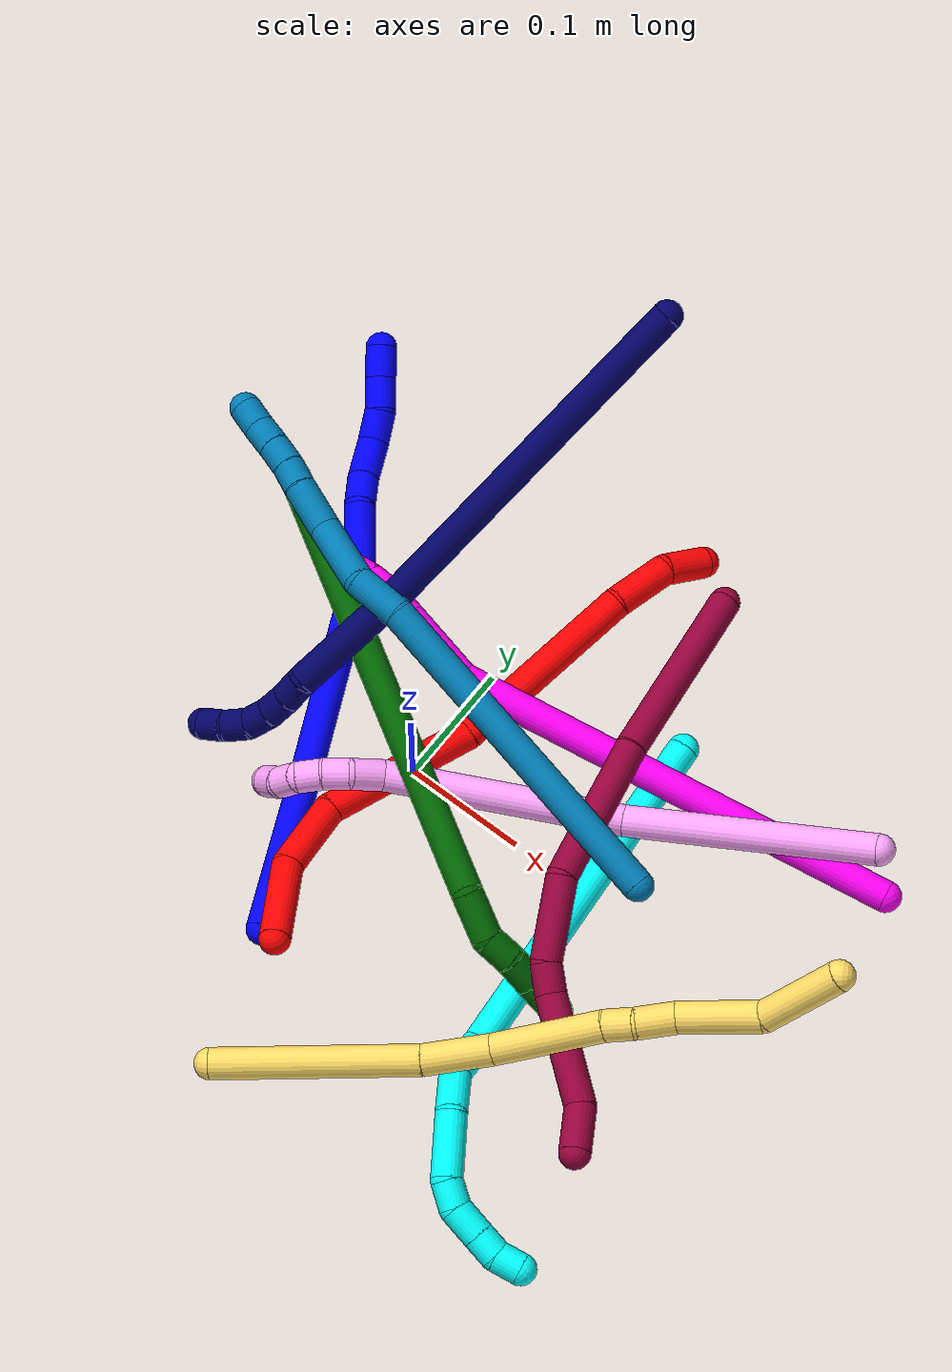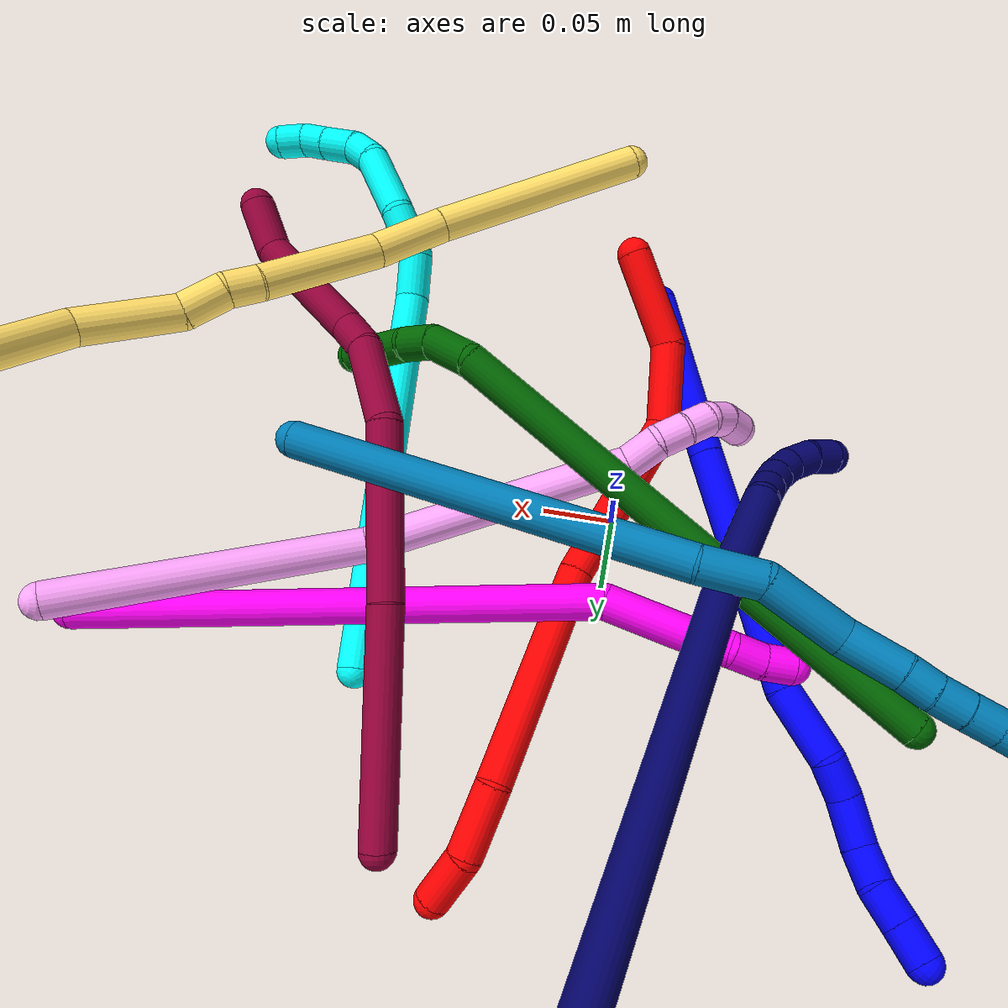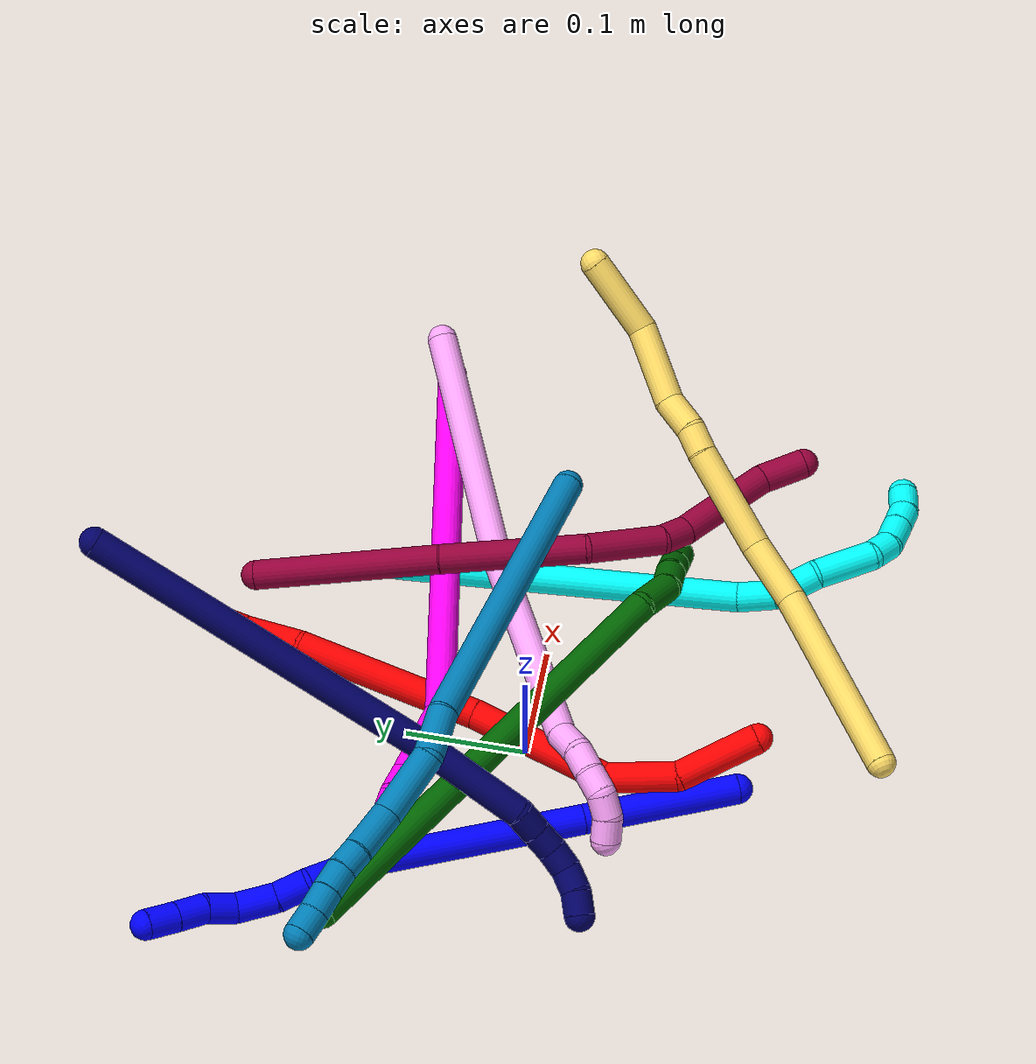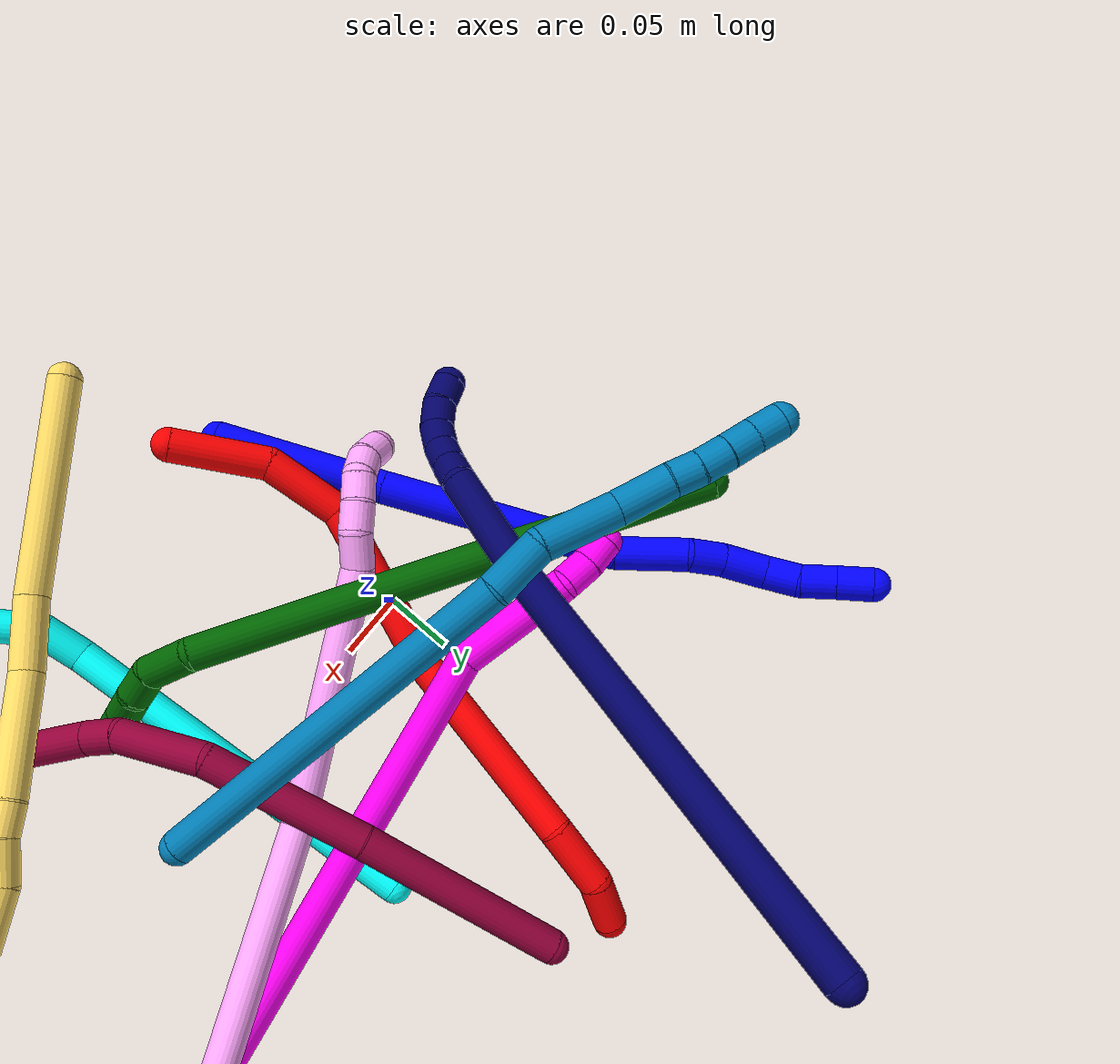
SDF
<sdf version="1.7">
 <world name="default">
  <plugin name="TubeGeneratorPlugin" filename="libtube_generator_plugin.so"/>
  <model name="photoneo_s_sensor">
   <static>1</static>
   <pose>0 0 2 1.57079 1.57079 3.14159</pose>
   <link name="link">
    <inertial><mass>0.1</mass></inertial>
    <sensor name="sensor" type="depth">
     <update_rate>30</update_rate>
     <camera>
      <horizontal_fov>1.22</horizontal_fov>
      <image><width>1920</width><height>1200</height><format>B8G8R8</format></image>
      <clip><near>0.1</near><far>2</far></clip>
      <depth_camera><output>points</output></depth_camera>
     </camera>
     <plugin name="camera_plugin" filename="libgazebo_ros_depth_camera.so">
      <baseline>0.2</baseline>
      <alwaysOn>1</alwaysOn>
      <updateRate>0.0</updateRate>
      <cameraName>camera_ir</cameraName>
      <imageTopicName>/camera/color/image_raw</imageTopicName>
      <cameraInfoTopicName>/camera/color/camera_info</cameraInfoTopicName>
      <depthImageTopicName>/camera/depth/image_raw</depthImageTopicName>
      <depthImageCameraInfoTopicName>/camera/depth/camera_info</depthImageCameraInfoTopicName>
      <pointCloudTopicName>/camera/depth/points</pointCloudTopicName>
      <frameName>fr_optical</frameName>
      <pointCloudCutoff>0.1</pointCloudCutoff>
      <pointCloudCutoffMax>2.0</pointCloudCutoffMax>
      <distortionK1>0</distortionK1>
      <distortionK2>0</distortionK2>
      <distortionK3>0</distortionK3>
      <distortionT1>0</distortionT1>
      <distortionT2>0</distortionT2>
      <CxPrime>0</CxPrime>
      <Cx>0</Cx>
      <Cy>0</Cy>
      <focalLength>0</focalLength>
      <hackBaseline>0</hackBaseline>
     </plugin>
    </sensor>
   </link>
  </model>
  <gravity>0 0 -9.8</gravity>
  <magnetic_field>6e-06 2.3e-05 -4.2e-05</magnetic_field>
  <atmosphere type="adiabatic"/>
  <physics name="default_physics" default="0" type="ode">
   <max_step_size>0.003</max_step_size>
   <real_time_factor>1</real_time_factor>
   <real_time_update_rate>1000</real_time_update_rate>
   <max_contacts>10000</max_contacts>
   <ode>
    <solver>
     <type>quick</type>
     <iters>100</iters>
     <sor>1.3</sor>
     <use_dynamic_moi_rescaling>0</use_dynamic_moi_rescaling>
    </solver>
    <constraints>
     <contact_max_correcting_vel>0</contact_max_correcting_vel>
     <contact_surface_layer>0.001</contact_surface_layer>
     <cfm>0</cfm>
     <erp>0.2</erp>
    </constraints>
   </ode>
  </physics>
  <scene><ambient>0.4 0.4 0.4 1</ambient><background>0.7 0.7 0.7 1</background><shadows>0</shadows></scene>
  <audio><device>default</device></audio>
  <spherical_coordinates>
   <surface_model>EARTH_WGS84</surface_model>
   <latitude_deg>0</latitude_deg>
   <longitude_deg>0</longitude_deg>
   <elevation>0</elevation>
   <heading_deg>0</heading_deg>
  </spherical_coordinates>
  <model name="bin">
   <static>1</static>
   <link name="bottom">
    <collision name="collision-bottom">
     <pose>0 0 -0.01 0 -0 0</pose>
     <geometry><box><size>0.8 0.6 0.02</size></box></geometry>
     <surface>
      <friction><ode><mu>100</mu><mu2>100</mu2></ode></friction>
      <contact><collide_bitmask>65535</collide_bitmask></contact>
     </surface>
    </collision>
   </link>
   <link name="west_wall">
    <collision name="collision-west_wall">
     <pose>-0.41 0 0.1 0 -0 0</pose>
     <geometry><box><size>0.02 0.6 0.2</size></box></geometry>
     <surface>
      <friction><ode><mu>100</mu><mu2>100</mu2></ode></friction>
      <contact><collide_bitmask>65535</collide_bitmask></contact>
     </surface>
    </collision>
   </link>
   <link name="east_wall">
    <collision name="collision-east_wall">
     <pose>0.41 0 0.1 0 -0 0</pose>
     <geometry><box><size>0.02 0.6 0.2</size></box></geometry>
     <surface>
      <friction><ode><mu>100</mu><mu2>100</mu2></ode></friction>
      <contact><collide_bitmask>65535</collide_bitmask></contact>
     </surface>
    </collision>
   </link>
   <link name="south_wall">
    <collision name="collision-south_wall">
     <pose>0 -0.31 0.1 0 -0 0</pose>
     <geometry><box><size>0.8 0.02 0.2</size></box></geometry>
     <surface>
      <friction><ode><mu>100</mu><mu2>100</mu2></ode></friction>
      <contact><collide_bitmask>65535</collide_bitmask></contact>
     </surface>
    </collision>
   </link>
   <link name="north_wall">
    <collision name="collision-north_wall">
     <pose>0 0.31 0.1 0 -0 0</pose>
     <geometry><box><size>0.8 0.02 0.2</size></box></geometry>
     <surface>
      <friction><ode><mu>100</mu><mu2>100</mu2></ode></friction>
      <contact><collide_bitmask>65535</collide_bitmask></contact>
     </surface>
    </collision>
   </link>
  </model>
  <model name="1">
   <static>0</static>
   <link name="1">
    <collision name="collision-cylinder-e_1_1_4">
     <pose>-0.016939 0.032809 0.05292 -0.554974 -0.265625 0.076071</pose>
     <geometry><cylinder><radius>0.0125</radius><length>0.129056</length></cylinder></geometry>
     <surface>
      <friction><ode><mu>1.16</mu><mu2>1.16</mu2><slip1>0</slip1><slip2>0</slip2></ode></friction>
      <contact><ode><kp>1e+06</kp><kd>1</kd><max_vel>0</max_vel><min_depth>0.001</min_depth></ode></contact>
     </surface>
    </collision>
    <visual name="visual-cylinder-e_1_1_4">
     <pose>-0.016939 0.032809 0.05292 -0.554974 -0.265625 0.076071</pose>
     <geometry><cylinder><radius>0.0125</radius><length>0.129056</length></cylinder></geometry>
     <material><ambient>0 0 1 1</ambient></material>
    </visual>
    <collision name="collision-cylinder-e_2_4_5">
     <pose>-0.055065 0.111319 0.180028 -0.552117 -0.238514 0.067865</pose>
     <geometry><cylinder><radius>0.0125</radius><length>0.179348</length></cylinder></geometry>
     <surface>
      <friction><ode><mu>1.16</mu><mu2>1.16</mu2><slip1>0</slip1><slip2>0</slip2></ode></friction>
      <contact><ode><kp>1e+06</kp><kd>1</kd><max_vel>0</max_vel><min_depth>0.001</min_depth></ode></contact>
     </surface>
    </collision>
    <visual name="visual-cylinder-e_2_4_5">
     <pose>-0.055065 0.111319 0.180028 -0.552117 -0.238514 0.067865</pose>
     <geometry><cylinder><radius>0.0125</radius><length>0.179348</length></cylinder></geometry>
     <material><ambient>0 0 1 1</ambient></material>
    </visual>
    <collision name="collision-cylinder-e_3_5_6">
     <pose>-0.077482 0.166369 0.279145 -0.358774 -0.046206 0.00838</pose>
     <geometry><cylinder><radius>0.0125</radius><length>0.053304</length></cylinder></geometry>
     <surface>
      <friction><ode><mu>1.16</mu><mu2>1.16</mu2><slip1>0</slip1><slip2>0</slip2></ode></friction>
      <contact><ode><kp>1e+06</kp><kd>1</kd><max_vel>0</max_vel><min_depth>0.001</min_depth></ode></contact>
     </surface>
    </collision>
    <visual name="visual-cylinder-e_3_5_6">
     <pose>-0.077482 0.166369 0.279145 -0.358774 -0.046206 0.00838</pose>
     <geometry><cylinder><radius>0.0125</radius><length>0.053304</length></cylinder></geometry>
     <material><ambient>0 0 1 1</ambient></material>
    </visual>
    <collision name="collision-cylinder-e_4_6_7">
     <pose>-0.08396 0.179466 0.315599 -0.314449 -0.408537 0.065659</pose>
     <geometry><cylinder><radius>0.0125</radius><length>0.026413</length></cylinder></geometry>
     <surface>
      <friction><ode><mu>1.16</mu><mu2>1.16</mu2><slip1>0</slip1><slip2>0</slip2></ode></friction>
      <contact><ode><kp>1e+06</kp><kd>1</kd><max_vel>0</max_vel><min_depth>0.001</min_depth></ode></contact>
     </surface>
    </collision>
    <visual name="visual-cylinder-e_4_6_7">
     <pose>-0.08396 0.179466 0.315599 -0.314449 -0.408537 0.065659</pose>
     <geometry><cylinder><radius>0.0125</radius><length>0.026413</length></cylinder></geometry>
     <material><ambient>0 0 1 1</ambient></material>
    </visual>
    <collision name="collision-cylinder-e_5_7_8">
     <pose>-0.094919 0.191103 0.34129 -0.508107 -0.338753 0.088755</pose>
     <geometry><cylinder><radius>0.0125</radius><length>0.034383</length></cylinder></geometry>
     <surface>
      <friction><ode><mu>1.16</mu><mu2>1.16</mu2><slip1>0</slip1><slip2>0</slip2></ode></friction>
      <contact><ode><kp>1e+06</kp><kd>1</kd><max_vel>0</max_vel><min_depth>0.001</min_depth></ode></contact>
     </surface>
    </collision>
    <visual name="visual-cylinder-e_5_7_8">
     <pose>-0.094919 0.191103 0.34129 -0.508107 -0.338753 0.088755</pose>
     <geometry><cylinder><radius>0.0125</radius><length>0.034383</length></cylinder></geometry>
     <material><ambient>0 0 1 1</ambient></material>
    </visual>
    <collision name="collision-cylinder-e_6_8_9">
     <pose>-0.099545 0.20709 0.365734 -0.667317 0.082847 -0.028731</pose>
     <geometry><cylinder><radius>0.0125</radius><length>0.02626</length></cylinder></geometry>
     <surface>
      <friction><ode><mu>1.16</mu><mu2>1.16</mu2><slip1>0</slip1><slip2>0</slip2></ode></friction>
      <contact><ode><kp>1e+06</kp><kd>1</kd><max_vel>0</max_vel><min_depth>0.001</min_depth></ode></contact>
     </surface>
    </collision>
    <visual name="visual-cylinder-e_6_8_9">
     <pose>-0.099545 0.20709 0.365734 -0.667317 0.082847 -0.028731</pose>
     <geometry><cylinder><radius>0.0125</radius><length>0.02626</length></cylinder></geometry>
     <material><ambient>0 0 1 1</ambient></material>
    </visual>
    <collision name="collision-cylinder-e_7_9_10">
     <pose>-0.097948 0.220291 0.387719 -0.411105 0.039987 -0.008338</pose>
     <geometry><cylinder><radius>0.0125</radius><length>0.025563</length></cylinder></geometry>
     <surface>
      <friction><ode><mu>1.16</mu><mu2>1.16</mu2><slip1>0</slip1><slip2>0</slip2></ode></friction>
      <contact><ode><kp>1e+06</kp><kd>1</kd><max_vel>0</max_vel><min_depth>0.001</min_depth></ode></contact>
     </surface>
    </collision>
    <visual name="visual-cylinder-e_7_9_10">
     <pose>-0.097948 0.220291 0.387719 -0.411105 0.039987 -0.008338</pose>
     <geometry><cylinder><radius>0.0125</radius><length>0.025563</length></cylinder></geometry>
     <material><ambient>0 0 1 1</ambient></material>
    </visual>
    <collision name="collision-cylinder-e_8_10_2">
     <pose>-0.096886 0.230856 0.41103 -0.43985 0.042924 -0.009597</pose>
     <geometry><cylinder><radius>0.0125</radius><length>0.025674</length></cylinder></geometry>
     <surface>
      <friction><ode><mu>1.16</mu><mu2>1.16</mu2><slip1>0</slip1><slip2>0</slip2></ode></friction>
      <contact><ode><kp>1e+06</kp><kd>1</kd><max_vel>0</max_vel><min_depth>0.001</min_depth></ode></contact>
     </surface>
    </collision>
    <visual name="visual-cylinder-e_8_10_2">
     <pose>-0.096886 0.230856 0.41103 -0.43985 0.042924 -0.009597</pose>
     <geometry><cylinder><radius>0.0125</radius><length>0.025674</length></cylinder></geometry>
     <material><ambient>0 0 1 1</ambient></material>
    </visual>
    <collision name="collision-sphere-2">
     <pose>-0.096335 0.236317 0.422635 0 -0 0</pose>
     <geometry><sphere><radius>0.0125</radius></sphere></geometry>
     <surface>
      <friction><ode><mu>1.16</mu><mu2>1.16</mu2><slip1>0</slip1><slip2>0</slip2></ode></friction>
      <contact><ode><kp>1e+06</kp><kd>1</kd><max_vel>0</max_vel><min_depth>0.001</min_depth></ode></contact>
     </surface>
    </collision>
    <visual name="visual-sphere-2">
     <pose>-0.096335 0.236317 0.422635 0 -0 0</pose>
     <geometry><sphere><radius>0.0125</radius></sphere></geometry>
     <material><ambient>0 0 1 1</ambient></material>
    </visual>
    <collision name="collision-sphere-10">
     <pose>-0.097437 0.225395 0.399426 0 -0 0</pose>
     <geometry><sphere><radius>0.0125</radius></sphere></geometry>
     <surface>
      <friction><ode><mu>1.16</mu><mu2>1.16</mu2><slip1>0</slip1><slip2>0</slip2></ode></friction>
      <contact><ode><kp>1e+06</kp><kd>1</kd><max_vel>0</max_vel><min_depth>0.001</min_depth></ode></contact>
     </surface>
    </collision>
    <visual name="visual-sphere-10">
     <pose>-0.097437 0.225395 0.399426 0 -0 0</pose>
     <geometry><sphere><radius>0.0125</radius></sphere></geometry>
     <material><ambient>0 0 1 1</ambient></material>
    </visual>
    <collision name="collision-sphere-9">
     <pose>-0.098459 0.215188 0.376012 0 -0 0</pose>
     <geometry><sphere><radius>0.0125</radius></sphere></geometry>
     <surface>
      <friction><ode><mu>1.16</mu><mu2>1.16</mu2><slip1>0</slip1><slip2>0</slip2></ode></friction>
      <contact><ode><kp>1e+06</kp><kd>1</kd><max_vel>0</max_vel><min_depth>0.001</min_depth></ode></contact>
     </surface>
    </collision>
    <visual name="visual-sphere-9">
     <pose>-0.098459 0.215188 0.376012 0 -0 0</pose>
     <geometry><sphere><radius>0.0125</radius></sphere></geometry>
     <material><ambient>0 0 1 1</ambient></material>
    </visual>
    <collision name="collision-sphere-4">
     <pose>-0.033879 0.065617 0.10584 0 -0 0</pose>
     <geometry><sphere><radius>0.0125</radius></sphere></geometry>
     <surface>
      <friction><ode><mu>1.16</mu><mu2>1.16</mu2><slip1>0</slip1><slip2>0</slip2></ode></friction>
      <contact><ode><kp>1e+06</kp><kd>1</kd><max_vel>0</max_vel><min_depth>0.001</min_depth></ode></contact>
     </surface>
    </collision>
    <visual name="visual-sphere-4">
     <pose>-0.033879 0.065617 0.10584 0 -0 0</pose>
     <geometry><sphere><radius>0.0125</radius></sphere></geometry>
     <material><ambient>0 0 1 1</ambient></material>
    </visual>
    <collision name="collision-sphere-1">
     <geometry><sphere><radius>0.0125</radius></sphere></geometry>
     <surface>
      <friction><ode><mu>1.16</mu><mu2>1.16</mu2><slip1>0</slip1><slip2>0</slip2></ode></friction>
      <contact><ode><kp>1e+06</kp><kd>1</kd><max_vel>0</max_vel><min_depth>0.001</min_depth></ode></contact>
     </surface>
    </collision>
    <visual name="visual-sphere-1">
     <geometry><sphere><radius>0.0125</radius></sphere></geometry>
     <material><ambient>0 0 1 1</ambient></material>
    </visual>
    <collision name="collision-sphere-8">
     <pose>-0.100632 0.198992 0.355456 0 -0 0</pose>
     <geometry><sphere><radius>0.0125</radius></sphere></geometry>
     <surface>
      <friction><ode><mu>1.16</mu><mu2>1.16</mu2><slip1>0</slip1><slip2>0</slip2></ode></friction>
      <contact><ode><kp>1e+06</kp><kd>1</kd><max_vel>0</max_vel><min_depth>0.001</min_depth></ode></contact>
     </surface>
    </collision>
    <visual name="visual-sphere-8">
     <pose>-0.100632 0.198992 0.355456 0 -0 0</pose>
     <geometry><sphere><radius>0.0125</radius></sphere></geometry>
     <material><ambient>0 0 1 1</ambient></material>
    </visual>
    <collision name="collision-sphere-5">
     <pose>-0.076251 0.157021 0.254216 0 -0 0</pose>
     <geometry><sphere><radius>0.0125</radius></sphere></geometry>
     <surface>
      <friction><ode><mu>1.16</mu><mu2>1.16</mu2><slip1>0</slip1><slip2>0</slip2></ode></friction>
      <contact><ode><kp>1e+06</kp><kd>1</kd><max_vel>0</max_vel><min_depth>0.001</min_depth></ode></contact>
     </surface>
    </collision>
    <visual name="visual-sphere-5">
     <pose>-0.076251 0.157021 0.254216 0 -0 0</pose>
     <geometry><sphere><radius>0.0125</radius></sphere></geometry>
     <material><ambient>0 0 1 1</ambient></material>
    </visual>
    <collision name="collision-sphere-6">
     <pose>-0.078713 0.175717 0.304073 0 -0 0</pose>
     <geometry><sphere><radius>0.0125</radius></sphere></geometry>
     <surface>
      <friction><ode><mu>1.16</mu><mu2>1.16</mu2><slip1>0</slip1><slip2>0</slip2></ode></friction>
      <contact><ode><kp>1e+06</kp><kd>1</kd><max_vel>0</max_vel><min_depth>0.001</min_depth></ode></contact>
     </surface>
    </collision>
    <visual name="visual-sphere-6">
     <pose>-0.078713 0.175717 0.304073 0 -0 0</pose>
     <geometry><sphere><radius>0.0125</radius></sphere></geometry>
     <material><ambient>0 0 1 1</ambient></material>
    </visual>
    <collision name="collision-sphere-7">
     <pose>-0.089206 0.183214 0.327124 0 -0 0</pose>
     <geometry><sphere><radius>0.0125</radius></sphere></geometry>
     <surface>
      <friction><ode><mu>1.16</mu><mu2>1.16</mu2><slip1>0</slip1><slip2>0</slip2></ode></friction>
      <contact><ode><kp>1e+06</kp><kd>1</kd><max_vel>0</max_vel><min_depth>0.001</min_depth></ode></contact>
     </surface>
    </collision>
    <visual name="visual-sphere-7">
     <pose>-0.089206 0.183214 0.327124 0 -0 0</pose>
     <geometry><sphere><radius>0.0125</radius></sphere></geometry>
     <material><ambient>0 0 1 1</ambient></material>
    </visual>
    <inertial>
     <pose>-0.058557 0.122749 0.20827 0 -0 0</pose>
     <mass>0.5</mass>
     <inertia>
      <ixx>0.000718</ixx>
      <ixy>0</ixy>
      <ixz>0</ixz>
      <iyy>0.000668</iyy>
      <iyz>0</iyz>
      <izz>-0.000154</izz>
     </inertia>
    </inertial>
   </link>
   <pose>-0.008986 -0.177223 0.011965 1.50026 -1.14169 -2.0556</pose>
  </model>
  <model name="2">
   <static>0</static>
   <link name="2">
    <collision name="collision-cylinder-e_1_1_4">
     <pose>0.025881 0.024058 -0.000377 -1.58645 0.821837 -0.833367</pose>
     <geometry><cylinder><radius>0.0125</radius><length>0.070676</length></cylinder></geometry>
     <surface>
      <friction><ode><mu>1.16</mu><mu2>1.16</mu2><slip1>0</slip1><slip2>0</slip2></ode></friction>
      <contact><ode><kp>1e+06</kp><kd>1</kd><max_vel>0</max_vel><min_depth>0.001</min_depth></ode></contact>
     </surface>
    </collision>
    <visual name="visual-cylinder-e_1_1_4">
     <pose>0.025881 0.024058 -0.000377 -1.58645 0.821837 -0.833367</pose>
     <geometry><cylinder><radius>0.0125</radius><length>0.070676</length></cylinder></geometry>
     <material><ambient>1 0 0 1</ambient></material>
    </visual>
    <collision name="collision-cylinder-e_2_4_5">
     <pose>0.062988 0.076024 0.000812 -1.51475 0.381852 -0.36149</pose>
     <geometry><cylinder><radius>0.0125</radius><length>0.060244</length></cylinder></geometry>
     <surface>
      <friction><ode><mu>1.16</mu><mu2>1.16</mu2><slip1>0</slip1><slip2>0</slip2></ode></friction>
      <contact><ode><kp>1e+06</kp><kd>1</kd><max_vel>0</max_vel><min_depth>0.001</min_depth></ode></contact>
     </surface>
    </collision>
    <visual name="visual-cylinder-e_2_4_5">
     <pose>0.062988 0.076024 0.000812 -1.51475 0.381852 -0.36149</pose>
     <geometry><cylinder><radius>0.0125</radius><length>0.060244</length></cylinder></geometry>
     <material><ambient>1 0 0 1</ambient></material>
    </visual>
    <collision name="collision-cylinder-e_3_5_6">
     <pose>0.068439 0.165699 0.011027 -1.43168 -0.092302 0.080292</pose>
     <geometry><cylinder><radius>0.0125</radius><length>0.12527</length></cylinder></geometry>
     <surface>
      <friction><ode><mu>1.16</mu><mu2>1.16</mu2><slip1>0</slip1><slip2>0</slip2></ode></friction>
      <contact><ode><kp>1e+06</kp><kd>1</kd><max_vel>0</max_vel><min_depth>0.001</min_depth></ode></contact>
     </surface>
    </collision>
    <visual name="visual-cylinder-e_3_5_6">
     <pose>0.068439 0.165699 0.011027 -1.43168 -0.092302 0.080292</pose>
     <geometry><cylinder><radius>0.0125</radius><length>0.12527</length></cylinder></geometry>
     <material><ambient>1 0 0 1</ambient></material>
    </visual>
    <collision name="collision-cylinder-e_4_6_7">
     <pose>0.062841 0.305413 0.0128 -1.65878 0.002239 -0.002446</pose>
     <geometry><cylinder><radius>0.0125</radius><length>0.156502</length></cylinder></geometry>
     <surface>
      <friction><ode><mu>1.16</mu><mu2>1.16</mu2><slip1>0</slip1><slip2>0</slip2></ode></friction>
      <contact><ode><kp>1e+06</kp><kd>1</kd><max_vel>0</max_vel><min_depth>0.001</min_depth></ode></contact>
     </surface>
    </collision>
    <visual name="visual-cylinder-e_4_6_7">
     <pose>0.062841 0.305413 0.0128 -1.65878 0.002239 -0.002446</pose>
     <geometry><cylinder><radius>0.0125</radius><length>0.156502</length></cylinder></geometry>
     <material><ambient>1 0 0 1</ambient></material>
    </visual>
    <collision name="collision-cylinder-e_5_7_8">
     <pose>0.064968 0.407691 0.009958 -1.40652 0.078974 -0.06697</pose>
     <geometry><cylinder><radius>0.0125</radius><length>0.049477</length></cylinder></geometry>
     <surface>
      <friction><ode><mu>1.16</mu><mu2>1.16</mu2><slip1>0</slip1><slip2>0</slip2></ode></friction>
      <contact><ode><kp>1e+06</kp><kd>1</kd><max_vel>0</max_vel><min_depth>0.001</min_depth></ode></contact>
     </surface>
    </collision>
    <visual name="visual-cylinder-e_5_7_8">
     <pose>0.064968 0.407691 0.009958 -1.40652 0.078974 -0.06697</pose>
     <geometry><cylinder><radius>0.0125</radius><length>0.049477</length></cylinder></geometry>
     <material><ambient>1 0 0 1</ambient></material>
    </visual>
    <collision name="collision-cylinder-e_6_8_2">
     <pose>0.066255 0.448138 0.023867 -1.02105 -0.035159 0.019692</pose>
     <geometry><cylinder><radius>0.0125</radius><length>0.037831</length></cylinder></geometry>
     <surface>
      <friction><ode><mu>1.16</mu><mu2>1.16</mu2><slip1>0</slip1><slip2>0</slip2></ode></friction>
      <contact><ode><kp>1e+06</kp><kd>1</kd><max_vel>0</max_vel><min_depth>0.001</min_depth></ode></contact>
     </surface>
    </collision>
    <visual name="visual-cylinder-e_6_8_2">
     <pose>0.066255 0.448138 0.023867 -1.02105 -0.035159 0.019692</pose>
     <geometry><cylinder><radius>0.0125</radius><length>0.037831</length></cylinder></geometry>
     <material><ambient>1 0 0 1</ambient></material>
    </visual>
    <collision name="collision-sphere-2">
     <pose>0.06559 0.464257 0.033744 0 -0 0</pose>
     <geometry><sphere><radius>0.0125</radius></sphere></geometry>
     <surface>
      <friction><ode><mu>1.16</mu><mu2>1.16</mu2><slip1>0</slip1><slip2>0</slip2></ode></friction>
      <contact><ode><kp>1e+06</kp><kd>1</kd><max_vel>0</max_vel><min_depth>0.001</min_depth></ode></contact>
     </surface>
    </collision>
    <visual name="visual-sphere-2">
     <pose>0.06559 0.464257 0.033744 0 -0 0</pose>
     <geometry><sphere><radius>0.0125</radius></sphere></geometry>
     <material><ambient>1 0 0 1</ambient></material>
    </visual>
    <collision name="collision-sphere-4">
     <pose>0.051763 0.048116 -0.000753 0 -0 0</pose>
     <geometry><sphere><radius>0.0125</radius></sphere></geometry>
     <surface>
      <friction><ode><mu>1.16</mu><mu2>1.16</mu2><slip1>0</slip1><slip2>0</slip2></ode></friction>
      <contact><ode><kp>1e+06</kp><kd>1</kd><max_vel>0</max_vel><min_depth>0.001</min_depth></ode></contact>
     </surface>
    </collision>
    <visual name="visual-sphere-4">
     <pose>0.051763 0.048116 -0.000753 0 -0 0</pose>
     <geometry><sphere><radius>0.0125</radius></sphere></geometry>
     <material><ambient>1 0 0 1</ambient></material>
    </visual>
    <collision name="collision-sphere-1">
     <geometry><sphere><radius>0.0125</radius></sphere></geometry>
     <surface>
      <friction><ode><mu>1.16</mu><mu2>1.16</mu2><slip1>0</slip1><slip2>0</slip2></ode></friction>
      <contact><ode><kp>1e+06</kp><kd>1</kd><max_vel>0</max_vel><min_depth>0.001</min_depth></ode></contact>
     </surface>
    </collision>
    <visual name="visual-sphere-1">
     <geometry><sphere><radius>0.0125</radius></sphere></geometry>
     <material><ambient>1 0 0 1</ambient></material>
    </visual>
    <collision name="collision-sphere-8">
     <pose>0.06692 0.43202 0.013991 0 -0 0</pose>
     <geometry><sphere><radius>0.0125</radius></sphere></geometry>
     <surface>
      <friction><ode><mu>1.16</mu><mu2>1.16</mu2><slip1>0</slip1><slip2>0</slip2></ode></friction>
      <contact><ode><kp>1e+06</kp><kd>1</kd><max_vel>0</max_vel><min_depth>0.001</min_depth></ode></contact>
     </surface>
    </collision>
    <visual name="visual-sphere-8">
     <pose>0.06692 0.43202 0.013991 0 -0 0</pose>
     <geometry><sphere><radius>0.0125</radius></sphere></geometry>
     <material><ambient>1 0 0 1</ambient></material>
    </visual>
    <collision name="collision-sphere-5">
     <pose>0.074212 0.103933 0.002378 0 -0 0</pose>
     <geometry><sphere><radius>0.0125</radius></sphere></geometry>
     <surface>
      <friction><ode><mu>1.16</mu><mu2>1.16</mu2><slip1>0</slip1><slip2>0</slip2></ode></friction>
      <contact><ode><kp>1e+06</kp><kd>1</kd><max_vel>0</max_vel><min_depth>0.001</min_depth></ode></contact>
     </surface>
    </collision>
    <visual name="visual-sphere-5">
     <pose>0.074212 0.103933 0.002378 0 -0 0</pose>
     <geometry><sphere><radius>0.0125</radius></sphere></geometry>
     <material><ambient>1 0 0 1</ambient></material>
    </visual>
    <collision name="collision-sphere-6">
     <pose>0.062666 0.227465 0.019676 0 -0 0</pose>
     <geometry><sphere><radius>0.0125</radius></sphere></geometry>
     <surface>
      <friction><ode><mu>1.16</mu><mu2>1.16</mu2><slip1>0</slip1><slip2>0</slip2></ode></friction>
      <contact><ode><kp>1e+06</kp><kd>1</kd><max_vel>0</max_vel><min_depth>0.001</min_depth></ode></contact>
     </surface>
    </collision>
    <visual name="visual-sphere-6">
     <pose>0.062666 0.227465 0.019676 0 -0 0</pose>
     <geometry><sphere><radius>0.0125</radius></sphere></geometry>
     <material><ambient>1 0 0 1</ambient></material>
    </visual>
    <collision name="collision-sphere-7">
     <pose>0.063016 0.383361 0.005924 0 -0 0</pose>
     <geometry><sphere><radius>0.0125</radius></sphere></geometry>
     <surface>
      <friction><ode><mu>1.16</mu><mu2>1.16</mu2><slip1>0</slip1><slip2>0</slip2></ode></friction>
      <contact><ode><kp>1e+06</kp><kd>1</kd><max_vel>0</max_vel><min_depth>0.001</min_depth></ode></contact>
     </surface>
    </collision>
    <visual name="visual-sphere-7">
     <pose>0.063016 0.383361 0.005924 0 -0 0</pose>
     <geometry><sphere><radius>0.0125</radius></sphere></geometry>
     <material><ambient>1 0 0 1</ambient></material>
    </visual>
    <inertial>
     <pose>0.059506 0.22392 0.009605 0 -0 0</pose>
     <mass>0.5</mass>
     <inertia>
      <ixx>0.000538</ixx>
      <ixy>0</ixy>
      <ixz>0</ixz>
      <iyy>4.7e-05</iyy>
      <iyz>0</iyz>
      <izz>-0.000563</izz>
     </inertia>
    </inertial>
   </link>
   <pose>0.014701 -0.187998 0.054633 3.10398 0.449294 2.90141</pose>
  </model>
  <model name="3">
   <static>0</static>
   <link name="3">
    <collision name="collision-cylinder-e_1_1_4">
     <pose>-0.004172 -0.099113 0.104186 0.760452 -0.029006 -0.011594</pose>
     <geometry><cylinder><radius>0.0125</radius><length>0.287719</length></cylinder></geometry>
     <surface>
      <friction><ode><mu>1.16</mu><mu2>1.16</mu2><slip1>0</slip1><slip2>0</slip2></ode></friction>
      <contact><ode><kp>1e+06</kp><kd>1</kd><max_vel>0</max_vel><min_depth>0.001</min_depth></ode></contact>
     </surface>
    </collision>
    <visual name="visual-cylinder-e_1_1_4">
     <pose>-0.004172 -0.099113 0.104186 0.760452 -0.029006 -0.011594</pose>
     <geometry><cylinder><radius>0.0125</radius><length>0.287719</length></cylinder></geometry>
     <material><ambient>0.003922 1 0.996078 1</ambient></material>
    </visual>
    <collision name="collision-cylinder-e_2_4_5">
     <pose>-0.0068 -0.212522 0.216945 1.03062 0.092385 0.052348</pose>
     <geometry><cylinder><radius>0.0125</radius><length>0.033481</length></cylinder></geometry>
     <surface>
      <friction><ode><mu>1.16</mu><mu2>1.16</mu2><slip1>0</slip1><slip2>0</slip2></ode></friction>
      <contact><ode><kp>1e+06</kp><kd>1</kd><max_vel>0</max_vel><min_depth>0.001</min_depth></ode></contact>
     </surface>
    </collision>
    <visual name="visual-cylinder-e_2_4_5">
     <pose>-0.0068 -0.212522 0.216945 1.03062 0.092385 0.052348</pose>
     <geometry><cylinder><radius>0.0125</radius><length>0.033481</length></cylinder></geometry>
     <material><ambient>0.003922 1 0.996078 1</ambient></material>
    </visual>
    <collision name="collision-cylinder-e_3_5_6">
     <pose>-0.011498 -0.24316 0.231 1.24711 -0.347484 -0.251159</pose>
     <geometry><cylinder><radius>0.0125</radius><length>0.036665</length></cylinder></geometry>
     <surface>
      <friction><ode><mu>1.16</mu><mu2>1.16</mu2><slip1>0</slip1><slip2>0</slip2></ode></friction>
      <contact><ode><kp>1e+06</kp><kd>1</kd><max_vel>0</max_vel><min_depth>0.001</min_depth></ode></contact>
     </surface>
    </collision>
    <visual name="visual-cylinder-e_3_5_6">
     <pose>-0.011498 -0.24316 0.231 1.24711 -0.347484 -0.251159</pose>
     <geometry><cylinder><radius>0.0125</radius><length>0.036665</length></cylinder></geometry>
     <material><ambient>0.003922 1 0.996078 1</ambient></material>
    </visual>
    <collision name="collision-cylinder-e_4_6_7">
     <pose>-0.030627 -0.278176 0.249543 0.960486 -0.514627 -0.272459</pose>
     <geometry><cylinder><radius>0.0125</radius><length>0.05236</length></cylinder></geometry>
     <surface>
      <friction><ode><mu>1.16</mu><mu2>1.16</mu2><slip1>0</slip1><slip2>0</slip2></ode></friction>
      <contact><ode><kp>1e+06</kp><kd>1</kd><max_vel>0</max_vel><min_depth>0.001</min_depth></ode></contact>
     </surface>
    </collision>
    <visual name="visual-cylinder-e_4_6_7">
     <pose>-0.030627 -0.278176 0.249543 0.960486 -0.514627 -0.272459</pose>
     <geometry><cylinder><radius>0.0125</radius><length>0.05236</length></cylinder></geometry>
     <material><ambient>0.003922 1 0.996078 1</ambient></material>
    </visual>
    <collision name="collision-cylinder-e_5_7_8">
     <pose>-0.052453 -0.301888 0.266778 0.878803 -0.93904 -0.468224</pose>
     <geometry><cylinder><radius>0.0125</radius><length>0.022155</length></cylinder></geometry>
     <surface>
      <friction><ode><mu>1.16</mu><mu2>1.16</mu2><slip1>0</slip1><slip2>0</slip2></ode></friction>
      <contact><ode><kp>1e+06</kp><kd>1</kd><max_vel>0</max_vel><min_depth>0.001</min_depth></ode></contact>
     </surface>
    </collision>
    <visual name="visual-cylinder-e_5_7_8">
     <pose>-0.052453 -0.301888 0.266778 0.878803 -0.93904 -0.468224</pose>
     <geometry><cylinder><radius>0.0125</radius><length>0.022155</length></cylinder></geometry>
     <material><ambient>0.003922 1 0.996078 1</ambient></material>
    </visual>
    <collision name="collision-cylinder-e_6_8_9">
     <pose>-0.074131 -0.310398 0.271531 1.40573 -1.30115 -1.14544</pose>
     <geometry><cylinder><radius>0.0125</radius><length>0.026433</length></cylinder></geometry>
     <surface>
      <friction><ode><mu>1.16</mu><mu2>1.16</mu2><slip1>0</slip1><slip2>0</slip2></ode></friction>
      <contact><ode><kp>1e+06</kp><kd>1</kd><max_vel>0</max_vel><min_depth>0.001</min_depth></ode></contact>
     </surface>
    </collision>
    <visual name="visual-cylinder-e_6_8_9">
     <pose>-0.074131 -0.310398 0.271531 1.40573 -1.30115 -1.14544</pose>
     <geometry><cylinder><radius>0.0125</radius><length>0.026433</length></cylinder></geometry>
     <material><ambient>0.003922 1 0.996078 1</ambient></material>
    </visual>
    <collision name="collision-cylinder-e_7_9_10">
     <pose>-0.096517 -0.316773 0.272332 1.49439 -1.27778 -1.20542</pose>
     <geometry><cylinder><radius>0.0125</radius><length>0.020154</length></cylinder></geometry>
     <surface>
      <friction><ode><mu>1.16</mu><mu2>1.16</mu2><slip1>0</slip1><slip2>0</slip2></ode></friction>
      <contact><ode><kp>1e+06</kp><kd>1</kd><max_vel>0</max_vel><min_depth>0.001</min_depth></ode></contact>
     </surface>
    </collision>
    <visual name="visual-cylinder-e_7_9_10">
     <pose>-0.096517 -0.316773 0.272332 1.49439 -1.27778 -1.20542</pose>
     <geometry><cylinder><radius>0.0125</radius><length>0.020154</length></cylinder></geometry>
     <material><ambient>0.003922 1 0.996078 1</ambient></material>
    </visual>
    <collision name="collision-cylinder-e_8_10_2">
     <pose>-0.116146 -0.321026 0.269531 2.72134 -1.2505 -2.56705</pose>
     <geometry><cylinder><radius>0.0125</radius><length>0.021034</length></cylinder></geometry>
     <surface>
      <friction><ode><mu>1.16</mu><mu2>1.16</mu2><slip1>0</slip1><slip2>0</slip2></ode></friction>
      <contact><ode><kp>1e+06</kp><kd>1</kd><max_vel>0</max_vel><min_depth>0.001</min_depth></ode></contact>
     </surface>
    </collision>
    <visual name="visual-cylinder-e_8_10_2">
     <pose>-0.116146 -0.321026 0.269531 2.72134 -1.2505 -2.56705</pose>
     <geometry><cylinder><radius>0.0125</radius><length>0.021034</length></cylinder></geometry>
     <material><ambient>0.003922 1 0.996078 1</ambient></material>
    </visual>
    <collision name="collision-sphere-2">
     <pose>-0.126128 -0.322377 0.266508 0 -0 0</pose>
     <geometry><sphere><radius>0.0125</radius></sphere></geometry>
     <surface>
      <friction><ode><mu>1.16</mu><mu2>1.16</mu2><slip1>0</slip1><slip2>0</slip2></ode></friction>
      <contact><ode><kp>1e+06</kp><kd>1</kd><max_vel>0</max_vel><min_depth>0.001</min_depth></ode></contact>
     </surface>
    </collision>
    <visual name="visual-sphere-2">
     <pose>-0.126128 -0.322377 0.266508 0 -0 0</pose>
     <geometry><sphere><radius>0.0125</radius></sphere></geometry>
     <material><ambient>0.003922 1 0.996078 1</ambient></material>
    </visual>
    <collision name="collision-sphere-10">
     <pose>-0.106164 -0.319675 0.272554 0 -0 0</pose>
     <geometry><sphere><radius>0.0125</radius></sphere></geometry>
     <surface>
      <friction><ode><mu>1.16</mu><mu2>1.16</mu2><slip1>0</slip1><slip2>0</slip2></ode></friction>
      <contact><ode><kp>1e+06</kp><kd>1</kd><max_vel>0</max_vel><min_depth>0.001</min_depth></ode></contact>
     </surface>
    </collision>
    <visual name="visual-sphere-10">
     <pose>-0.106164 -0.319675 0.272554 0 -0 0</pose>
     <geometry><sphere><radius>0.0125</radius></sphere></geometry>
     <material><ambient>0.003922 1 0.996078 1</ambient></material>
    </visual>
    <collision name="collision-sphere-9">
     <pose>-0.086869 -0.313871 0.272109 0 -0 0</pose>
     <geometry><sphere><radius>0.0125</radius></sphere></geometry>
     <surface>
      <friction><ode><mu>1.16</mu><mu2>1.16</mu2><slip1>0</slip1><slip2>0</slip2></ode></friction>
      <contact><ode><kp>1e+06</kp><kd>1</kd><max_vel>0</max_vel><min_depth>0.001</min_depth></ode></contact>
     </surface>
    </collision>
    <visual name="visual-sphere-9">
     <pose>-0.086869 -0.313871 0.272109 0 -0 0</pose>
     <geometry><sphere><radius>0.0125</radius></sphere></geometry>
     <material><ambient>0.003922 1 0.996078 1</ambient></material>
    </visual>
    <collision name="collision-sphere-4">
     <pose>-0.008344 -0.198226 0.208372 0 -0 0</pose>
     <geometry><sphere><radius>0.0125</radius></sphere></geometry>
     <surface>
      <friction><ode><mu>1.16</mu><mu2>1.16</mu2><slip1>0</slip1><slip2>0</slip2></ode></friction>
      <contact><ode><kp>1e+06</kp><kd>1</kd><max_vel>0</max_vel><min_depth>0.001</min_depth></ode></contact>
     </surface>
    </collision>
    <visual name="visual-sphere-4">
     <pose>-0.008344 -0.198226 0.208372 0 -0 0</pose>
     <geometry><sphere><radius>0.0125</radius></sphere></geometry>
     <material><ambient>0.003922 1 0.996078 1</ambient></material>
    </visual>
    <collision name="collision-sphere-1">
     <geometry><sphere><radius>0.0125</radius></sphere></geometry>
     <surface>
      <friction><ode><mu>1.16</mu><mu2>1.16</mu2><slip1>0</slip1><slip2>0</slip2></ode></friction>
      <contact><ode><kp>1e+06</kp><kd>1</kd><max_vel>0</max_vel><min_depth>0.001</min_depth></ode></contact>
     </surface>
    </collision>
    <visual name="visual-sphere-1">
     <geometry><sphere><radius>0.0125</radius></sphere></geometry>
     <material><ambient>0.003922 1 0.996078 1</ambient></material>
    </visual>
    <collision name="collision-sphere-8">
     <pose>-0.061392 -0.306925 0.270952 0 -0 0</pose>
     <geometry><sphere><radius>0.0125</radius></sphere></geometry>
     <surface>
      <friction><ode><mu>1.16</mu><mu2>1.16</mu2><slip1>0</slip1><slip2>0</slip2></ode></friction>
      <contact><ode><kp>1e+06</kp><kd>1</kd><max_vel>0</max_vel><min_depth>0.001</min_depth></ode></contact>
     </surface>
    </collision>
    <visual name="visual-sphere-8">
     <pose>-0.061392 -0.306925 0.270952 0 -0 0</pose>
     <geometry><sphere><radius>0.0125</radius></sphere></geometry>
     <material><ambient>0.003922 1 0.996078 1</ambient></material>
    </visual>
    <collision name="collision-sphere-5">
     <pose>-0.005256 -0.226818 0.225517 0 -0 0</pose>
     <geometry><sphere><radius>0.0125</radius></sphere></geometry>
     <surface>
      <friction><ode><mu>1.16</mu><mu2>1.16</mu2><slip1>0</slip1><slip2>0</slip2></ode></friction>
      <contact><ode><kp>1e+06</kp><kd>1</kd><max_vel>0</max_vel><min_depth>0.001</min_depth></ode></contact>
     </surface>
    </collision>
    <visual name="visual-sphere-5">
     <pose>-0.005256 -0.226818 0.225517 0 -0 0</pose>
     <geometry><sphere><radius>0.0125</radius></sphere></geometry>
     <material><ambient>0.003922 1 0.996078 1</ambient></material>
    </visual>
    <collision name="collision-sphere-6">
     <pose>-0.017741 -0.259501 0.236482 0 -0 0</pose>
     <geometry><sphere><radius>0.0125</radius></sphere></geometry>
     <surface>
      <friction><ode><mu>1.16</mu><mu2>1.16</mu2><slip1>0</slip1><slip2>0</slip2></ode></friction>
      <contact><ode><kp>1e+06</kp><kd>1</kd><max_vel>0</max_vel><min_depth>0.001</min_depth></ode></contact>
     </surface>
    </collision>
    <visual name="visual-sphere-6">
     <pose>-0.017741 -0.259501 0.236482 0 -0 0</pose>
     <geometry><sphere><radius>0.0125</radius></sphere></geometry>
     <material><ambient>0.003922 1 0.996078 1</ambient></material>
    </visual>
    <collision name="collision-sphere-7">
     <pose>-0.043513 -0.296851 0.262604 0 -0 0</pose>
     <geometry><sphere><radius>0.0125</radius></sphere></geometry>
     <surface>
      <friction><ode><mu>1.16</mu><mu2>1.16</mu2><slip1>0</slip1><slip2>0</slip2></ode></friction>
      <contact><ode><kp>1e+06</kp><kd>1</kd><max_vel>0</max_vel><min_depth>0.001</min_depth></ode></contact>
     </surface>
    </collision>
    <visual name="visual-sphere-7">
     <pose>-0.043513 -0.296851 0.262604 0 -0 0</pose>
     <geometry><sphere><radius>0.0125</radius></sphere></geometry>
     <material><ambient>0.003922 1 0.996078 1</ambient></material>
    </visual>
    <inertial>
     <pose>-0.021926 -0.174285 0.166042 0 -0 0</pose>
     <mass>0.5</mass>
     <inertia>
      <ixx>0.001978</ixx>
      <ixy>0</ixy>
      <ixz>0</ixz>
      <iyy>0.001413</iyy>
      <iyz>0</iyz>
      <izz>0.00149</izz>
     </inertia>
    </inertial>
   </link>
   <pose>0.157979 0.138768 0.012806 -2.32209 -0.412264 -3.09787</pose>
  </model>
  <model name="4">
   <static>0</static>
   <link name="4">
    <collision name="collision-cylinder-e_1_1_4">
     <pose>-0.040599 -0.037616 -0.085343 2.72645 -0.41057 -1.55939</pose>
     <geometry><cylinder><radius>0.0125</radius><length>0.203438</length></cylinder></geometry>
     <surface>
      <friction><ode><mu>1.16</mu><mu2>1.16</mu2><slip1>0</slip1><slip2>0</slip2></ode></friction>
      <contact><ode><kp>1e+06</kp><kd>1</kd><max_vel>0</max_vel><min_depth>0.001</min_depth></ode></contact>
     </surface>
    </collision>
    <visual name="visual-cylinder-e_1_1_4">
     <pose>-0.040599 -0.037616 -0.085343 2.72645 -0.41057 -1.55939</pose>
     <geometry><cylinder><radius>0.0125</radius><length>0.203438</length></cylinder></geometry>
     <material><ambient>1 0.65098 0.996078 1</ambient></material>
    </visual>
    <collision name="collision-cylinder-e_2_4_5">
     <pose>-0.125212 -0.132157 -0.231897 2.39246 -0.484654 -1.12261</pose>
     <geometry><cylinder><radius>0.0125</radius><length>0.188938</length></cylinder></geometry>
     <surface>
      <friction><ode><mu>1.16</mu><mu2>1.16</mu2><slip1>0</slip1><slip2>0</slip2></ode></friction>
      <contact><ode><kp>1e+06</kp><kd>1</kd><max_vel>0</max_vel><min_depth>0.001</min_depth></ode></contact>
     </surface>
    </collision>
    <visual name="visual-cylinder-e_2_4_5">
     <pose>-0.125212 -0.132157 -0.231897 2.39246 -0.484654 -1.12261</pose>
     <geometry><cylinder><radius>0.0125</radius><length>0.188938</length></cylinder></geometry>
     <material><ambient>1 0.65098 0.996078 1</ambient></material>
    </visual>
    <collision name="collision-cylinder-e_3_5_6">
     <pose>-0.173076 -0.200207 -0.298857 2.04776 -0.298313 -0.483942</pose>
     <geometry><cylinder><radius>0.0125</radius><length>0.026204</length></cylinder></geometry>
     <surface>
      <friction><ode><mu>1.16</mu><mu2>1.16</mu2><slip1>0</slip1><slip2>0</slip2></ode></friction>
      <contact><ode><kp>1e+06</kp><kd>1</kd><max_vel>0</max_vel><min_depth>0.001</min_depth></ode></contact>
     </surface>
    </collision>
    <visual name="visual-cylinder-e_3_5_6">
     <pose>-0.173076 -0.200207 -0.298857 2.04776 -0.298313 -0.483942</pose>
     <geometry><cylinder><radius>0.0125</radius><length>0.026204</length></cylinder></geometry>
     <material><ambient>1 0.65098 0.996078 1</ambient></material>
    </visual>
    <collision name="collision-cylinder-e_4_6_7">
     <pose>-0.180047 -0.217853 -0.312419 2.44613 -0.297525 -0.784147</pose>
     <geometry><cylinder><radius>0.0125</radius><length>0.021287</length></cylinder></geometry>
     <surface>
      <friction><ode><mu>1.16</mu><mu2>1.16</mu2><slip1>0</slip1><slip2>0</slip2></ode></friction>
      <contact><ode><kp>1e+06</kp><kd>1</kd><max_vel>0</max_vel><min_depth>0.001</min_depth></ode></contact>
     </surface>
    </collision>
    <visual name="visual-cylinder-e_4_6_7">
     <pose>-0.180047 -0.217853 -0.312419 2.44613 -0.297525 -0.784147</pose>
     <geometry><cylinder><radius>0.0125</radius><length>0.021287</length></cylinder></geometry>
     <material><ambient>1 0.65098 0.996078 1</ambient></material>
    </visual>
    <collision name="collision-cylinder-e_5_7_8">
     <pose>-0.18494 -0.229436 -0.32871 2.60325 -0.177667 -0.624608</pose>
     <geometry><cylinder><radius>0.0125</radius><length>0.020067</length></cylinder></geometry>
     <surface>
      <friction><ode><mu>1.16</mu><mu2>1.16</mu2><slip1>0</slip1><slip2>0</slip2></ode></friction>
      <contact><ode><kp>1e+06</kp><kd>1</kd><max_vel>0</max_vel><min_depth>0.001</min_depth></ode></contact>
     </surface>
    </collision>
    <visual name="visual-cylinder-e_5_7_8">
     <pose>-0.18494 -0.229436 -0.32871 2.60325 -0.177667 -0.624608</pose>
     <geometry><cylinder><radius>0.0125</radius><length>0.020067</length></cylinder></geometry>
     <material><ambient>1 0.65098 0.996078 1</ambient></material>
    </visual>
    <collision name="collision-cylinder-e_6_8_9">
     <pose>-0.187485 -0.234731 -0.347172 3.1184 -0.077126 -2.55754</pose>
     <geometry><cylinder><radius>0.0125</radius><length>0.02003</length></cylinder></geometry>
     <surface>
      <friction><ode><mu>1.16</mu><mu2>1.16</mu2><slip1>0</slip1><slip2>0</slip2></ode></friction>
      <contact><ode><kp>1e+06</kp><kd>1</kd><max_vel>0</max_vel><min_depth>0.001</min_depth></ode></contact>
     </surface>
    </collision>
    <visual name="visual-cylinder-e_6_8_9">
     <pose>-0.187485 -0.234731 -0.347172 3.1184 -0.077126 -2.55754</pose>
     <geometry><cylinder><radius>0.0125</radius><length>0.02003</length></cylinder></geometry>
     <material><ambient>1 0.65098 0.996078 1</ambient></material>
    </visual>
    <collision name="collision-cylinder-e_7_9_2">
     <pose>-0.190897 -0.232187 -0.366411 -2.85026 -0.266661 1.48127</pose>
     <geometry><cylinder><radius>0.0125</radius><length>0.020037</length></cylinder></geometry>
     <surface>
      <friction><ode><mu>1.16</mu><mu2>1.16</mu2><slip1>0</slip1><slip2>0</slip2></ode></friction>
      <contact><ode><kp>1e+06</kp><kd>1</kd><max_vel>0</max_vel><min_depth>0.001</min_depth></ode></contact>
     </surface>
    </collision>
    <visual name="visual-cylinder-e_7_9_2">
     <pose>-0.190897 -0.232187 -0.366411 -2.85026 -0.266661 1.48127</pose>
     <geometry><cylinder><radius>0.0125</radius><length>0.020037</length></cylinder></geometry>
     <material><ambient>1 0.65098 0.996078 1</ambient></material>
    </visual>
    <collision name="collision-sphere-2">
     <pose>-0.193537 -0.229411 -0.375668 0 -0 0</pose>
     <geometry><sphere><radius>0.0125</radius></sphere></geometry>
     <surface>
      <friction><ode><mu>1.16</mu><mu2>1.16</mu2><slip1>0</slip1><slip2>0</slip2></ode></friction>
      <contact><ode><kp>1e+06</kp><kd>1</kd><max_vel>0</max_vel><min_depth>0.001</min_depth></ode></contact>
     </surface>
    </collision>
    <visual name="visual-sphere-2">
     <pose>-0.193537 -0.229411 -0.375668 0 -0 0</pose>
     <geometry><sphere><radius>0.0125</radius></sphere></geometry>
     <material><ambient>1 0.65098 0.996078 1</ambient></material>
    </visual>
    <collision name="collision-sphere-9">
     <pose>-0.188257 -0.234963 -0.357154 0 -0 0</pose>
     <geometry><sphere><radius>0.0125</radius></sphere></geometry>
     <surface>
      <friction><ode><mu>1.16</mu><mu2>1.16</mu2><slip1>0</slip1><slip2>0</slip2></ode></friction>
      <contact><ode><kp>1e+06</kp><kd>1</kd><max_vel>0</max_vel><min_depth>0.001</min_depth></ode></contact>
     </surface>
    </collision>
    <visual name="visual-sphere-9">
     <pose>-0.188257 -0.234963 -0.357154 0 -0 0</pose>
     <geometry><sphere><radius>0.0125</radius></sphere></geometry>
     <material><ambient>1 0.65098 0.996078 1</ambient></material>
    </visual>
    <collision name="collision-sphere-4">
     <pose>-0.081199 -0.075233 -0.170686 0 -0 0</pose>
     <geometry><sphere><radius>0.0125</radius></sphere></geometry>
     <surface>
      <friction><ode><mu>1.16</mu><mu2>1.16</mu2><slip1>0</slip1><slip2>0</slip2></ode></friction>
      <contact><ode><kp>1e+06</kp><kd>1</kd><max_vel>0</max_vel><min_depth>0.001</min_depth></ode></contact>
     </surface>
    </collision>
    <visual name="visual-sphere-4">
     <pose>-0.081199 -0.075233 -0.170686 0 -0 0</pose>
     <geometry><sphere><radius>0.0125</radius></sphere></geometry>
     <material><ambient>1 0.65098 0.996078 1</ambient></material>
    </visual>
    <collision name="collision-sphere-1">
     <geometry><sphere><radius>0.0125</radius></sphere></geometry>
     <surface>
      <friction><ode><mu>1.16</mu><mu2>1.16</mu2><slip1>0</slip1><slip2>0</slip2></ode></friction>
      <contact><ode><kp>1e+06</kp><kd>1</kd><max_vel>0</max_vel><min_depth>0.001</min_depth></ode></contact>
     </surface>
    </collision>
    <visual name="visual-sphere-1">
     <geometry><sphere><radius>0.0125</radius></sphere></geometry>
     <material><ambient>1 0.65098 0.996078 1</ambient></material>
    </visual>
    <collision name="collision-sphere-8">
     <pose>-0.186713 -0.2345 -0.337189 0 -0 0</pose>
     <geometry><sphere><radius>0.0125</radius></sphere></geometry>
     <surface>
      <friction><ode><mu>1.16</mu><mu2>1.16</mu2><slip1>0</slip1><slip2>0</slip2></ode></friction>
      <contact><ode><kp>1e+06</kp><kd>1</kd><max_vel>0</max_vel><min_depth>0.001</min_depth></ode></contact>
     </surface>
    </collision>
    <visual name="visual-sphere-8">
     <pose>-0.186713 -0.2345 -0.337189 0 -0 0</pose>
     <geometry><sphere><radius>0.0125</radius></sphere></geometry>
     <material><ambient>1 0.65098 0.996078 1</ambient></material>
    </visual>
    <collision name="collision-sphere-5">
     <pose>-0.169225 -0.189082 -0.293108 0 -0 0</pose>
     <geometry><sphere><radius>0.0125</radius></sphere></geometry>
     <surface>
      <friction><ode><mu>1.16</mu><mu2>1.16</mu2><slip1>0</slip1><slip2>0</slip2></ode></friction>
      <contact><ode><kp>1e+06</kp><kd>1</kd><max_vel>0</max_vel><min_depth>0.001</min_depth></ode></contact>
     </surface>
    </collision>
    <visual name="visual-sphere-5">
     <pose>-0.169225 -0.189082 -0.293108 0 -0 0</pose>
     <geometry><sphere><radius>0.0125</radius></sphere></geometry>
     <material><ambient>1 0.65098 0.996078 1</ambient></material>
    </visual>
    <collision name="collision-sphere-6">
     <pose>-0.176926 -0.211333 -0.304606 0 -0 0</pose>
     <geometry><sphere><radius>0.0125</radius></sphere></geometry>
     <surface>
      <friction><ode><mu>1.16</mu><mu2>1.16</mu2><slip1>0</slip1><slip2>0</slip2></ode></friction>
      <contact><ode><kp>1e+06</kp><kd>1</kd><max_vel>0</max_vel><min_depth>0.001</min_depth></ode></contact>
     </surface>
    </collision>
    <visual name="visual-sphere-6">
     <pose>-0.176926 -0.211333 -0.304606 0 -0 0</pose>
     <geometry><sphere><radius>0.0125</radius></sphere></geometry>
     <material><ambient>1 0.65098 0.996078 1</ambient></material>
    </visual>
    <collision name="collision-sphere-7">
     <pose>-0.183167 -0.224373 -0.320231 0 -0 0</pose>
     <geometry><sphere><radius>0.0125</radius></sphere></geometry>
     <surface>
      <friction><ode><mu>1.16</mu><mu2>1.16</mu2><slip1>0</slip1><slip2>0</slip2></ode></friction>
      <contact><ode><kp>1e+06</kp><kd>1</kd><max_vel>0</max_vel><min_depth>0.001</min_depth></ode></contact>
     </surface>
    </collision>
    <visual name="visual-sphere-7">
     <pose>-0.183167 -0.224373 -0.320231 0 -0 0</pose>
     <geometry><sphere><radius>0.0125</radius></sphere></geometry>
     <material><ambient>1 0.65098 0.996078 1</ambient></material>
    </visual>
    <inertial>
     <pose>-0.103152 -0.112928 -0.193099 0 -0 0</pose>
     <mass>0.5</mass>
     <inertia>
      <ixx>-0.000893</ixx>
      <ixy>0</ixy>
      <ixz>0</ixz>
      <iyy>-0.001037</iyy>
      <iyz>0</iyz>
      <izz>0.00113</izz>
     </inertia>
    </inertial>
   </link>
   <pose>0.34142 0.137301 0.092248 -0.711326 0.284828 -0.603546</pose>
  </model>
  <model name="5">
   <static>0</static>
   <link name="5">
    <collision name="collision-cylinder-e_1_1_4">
     <pose>0.004773 -0.003279 0.081285 0.040319 0.058605 0.001182</pose>
     <geometry><cylinder><radius>0.0125</radius><length>0.162982</length></cylinder></geometry>
     <surface>
      <friction><ode><mu>1.16</mu><mu2>1.16</mu2><slip1>0</slip1><slip2>0</slip2></ode></friction>
      <contact><ode><kp>1e+06</kp><kd>1</kd><max_vel>0</max_vel><min_depth>0.001</min_depth></ode></contact>
     </surface>
    </collision>
    <visual name="visual-cylinder-e_1_1_4">
     <pose>0.004773 -0.003279 0.081285 0.040319 0.058605 0.001182</pose>
     <geometry><cylinder><radius>0.0125</radius><length>0.162982</length></cylinder></geometry>
     <material><ambient>1 0.858824 0.4 1</ambient></material>
    </visual>
    <collision name="collision-cylinder-e_2_4_5">
     <pose>0.014854 -0.007704 0.189543 0.042445 0.194151 0.004134</pose>
     <geometry><cylinder><radius>0.0125</radius><length>0.055028</length></cylinder></geometry>
     <surface>
      <friction><ode><mu>1.16</mu><mu2>1.16</mu2><slip1>0</slip1><slip2>0</slip2></ode></friction>
      <contact><ode><kp>1e+06</kp><kd>1</kd><max_vel>0</max_vel><min_depth>0.001</min_depth></ode></contact>
     </surface>
    </collision>
    <visual name="visual-cylinder-e_2_4_5">
     <pose>0.014854 -0.007704 0.189543 0.042445 0.194151 0.004134</pose>
     <geometry><cylinder><radius>0.0125</radius><length>0.055028</length></cylinder></geometry>
     <material><ambient>1 0.858824 0.4 1</ambient></material>
    </visual>
    <collision name="collision-cylinder-e_3_5_6">
     <pose>0.032974 -0.004373 0.259548 -0.103659 0.287884 -0.015038</pose>
     <geometry><cylinder><radius>0.0125</radius><length>0.090243</length></cylinder></geometry>
     <surface>
      <friction><ode><mu>1.16</mu><mu2>1.16</mu2><slip1>0</slip1><slip2>0</slip2></ode></friction>
      <contact><ode><kp>1e+06</kp><kd>1</kd><max_vel>0</max_vel><min_depth>0.001</min_depth></ode></contact>
     </surface>
    </collision>
    <visual name="visual-cylinder-e_3_5_6">
     <pose>0.032974 -0.004373 0.259548 -0.103659 0.287884 -0.015038</pose>
     <geometry><cylinder><radius>0.0125</radius><length>0.090243</length></cylinder></geometry>
     <material><ambient>1 0.858824 0.4 1</ambient></material>
    </visual>
    <collision name="collision-cylinder-e_4_6_7">
     <pose>0.04756 0.001358 0.314175 -0.10776 0.151076 -0.008163</pose>
     <geometry><cylinder><radius>0.0125</radius><length>0.023592</length></cylinder></geometry>
     <surface>
      <friction><ode><mu>1.16</mu><mu2>1.16</mu2><slip1>0</slip1><slip2>0</slip2></ode></friction>
      <contact><ode><kp>1e+06</kp><kd>1</kd><max_vel>0</max_vel><min_depth>0.001</min_depth></ode></contact>
     </surface>
    </collision>
    <visual name="visual-cylinder-e_4_6_7">
     <pose>0.04756 0.001358 0.314175 -0.10776 0.151076 -0.008163</pose>
     <geometry><cylinder><radius>0.0125</radius><length>0.023592</length></cylinder></geometry>
     <material><ambient>1 0.858824 0.4 1</ambient></material>
    </visual>
    <collision name="collision-cylinder-e_5_7_8">
     <pose>0.051778 0.00014 0.341178 0.159126 0.155247 0.012403</pose>
     <geometry><cylinder><radius>0.0125</radius><length>0.031592</length></cylinder></geometry>
     <surface>
      <friction><ode><mu>1.16</mu><mu2>1.16</mu2><slip1>0</slip1><slip2>0</slip2></ode></friction>
      <contact><ode><kp>1e+06</kp><kd>1</kd><max_vel>0</max_vel><min_depth>0.001</min_depth></ode></contact>
     </surface>
    </collision>
    <visual name="visual-cylinder-e_5_7_8">
     <pose>0.051778 0.00014 0.341178 0.159126 0.155247 0.012403</pose>
     <geometry><cylinder><radius>0.0125</radius><length>0.031592</length></cylinder></geometry>
     <material><ambient>1 0.858824 0.4 1</ambient></material>
    </visual>
    <collision name="collision-cylinder-e_6_8_9">
     <pose>0.058021 0.003551 0.389868 -0.174984 0.111983 -0.009833</pose>
     <geometry><cylinder><radius>0.0125</radius><length>0.068021</length></cylinder></geometry>
     <surface>
      <friction><ode><mu>1.16</mu><mu2>1.16</mu2><slip1>0</slip1><slip2>0</slip2></ode></friction>
      <contact><ode><kp>1e+06</kp><kd>1</kd><max_vel>0</max_vel><min_depth>0.001</min_depth></ode></contact>
     </surface>
    </collision>
    <visual name="visual-cylinder-e_6_8_9">
     <pose>0.058021 0.003551 0.389868 -0.174984 0.111983 -0.009833</pose>
     <geometry><cylinder><radius>0.0125</radius><length>0.068021</length></cylinder></geometry>
     <material><ambient>1 0.858824 0.4 1</ambient></material>
    </visual>
    <collision name="collision-cylinder-e_7_9_2">
     <pose>0.080484 0.015685 0.451205 -0.219187 0.575849 -0.065151</pose>
     <geometry><cylinder><radius>0.0125</radius><length>0.068542</length></cylinder></geometry>
     <surface>
      <friction><ode><mu>1.16</mu><mu2>1.16</mu2><slip1>0</slip1><slip2>0</slip2></ode></friction>
      <contact><ode><kp>1e+06</kp><kd>1</kd><max_vel>0</max_vel><min_depth>0.001</min_depth></ode></contact>
     </surface>
    </collision>
    <visual name="visual-cylinder-e_7_9_2">
     <pose>0.080484 0.015685 0.451205 -0.219187 0.575849 -0.065151</pose>
     <geometry><cylinder><radius>0.0125</radius><length>0.068542</length></cylinder></geometry>
     <material><ambient>1 0.858824 0.4 1</ambient></material>
    </visual>
    <collision name="collision-sphere-2">
     <pose>0.099146 0.021935 0.479262 0 -0 0</pose>
     <geometry><sphere><radius>0.0125</radius></sphere></geometry>
     <surface>
      <friction><ode><mu>1.16</mu><mu2>1.16</mu2><slip1>0</slip1><slip2>0</slip2></ode></friction>
      <contact><ode><kp>1e+06</kp><kd>1</kd><max_vel>0</max_vel><min_depth>0.001</min_depth></ode></contact>
     </surface>
    </collision>
    <visual name="visual-sphere-2">
     <pose>0.099146 0.021935 0.479262 0 -0 0</pose>
     <geometry><sphere><radius>0.0125</radius></sphere></geometry>
     <material><ambient>1 0.858824 0.4 1</ambient></material>
    </visual>
    <collision name="collision-sphere-9">
     <pose>0.061822 0.009435 0.423149 0 -0 0</pose>
     <geometry><sphere><radius>0.0125</radius></sphere></geometry>
     <surface>
      <friction><ode><mu>1.16</mu><mu2>1.16</mu2><slip1>0</slip1><slip2>0</slip2></ode></friction>
      <contact><ode><kp>1e+06</kp><kd>1</kd><max_vel>0</max_vel><min_depth>0.001</min_depth></ode></contact>
     </surface>
    </collision>
    <visual name="visual-sphere-9">
     <pose>0.061822 0.009435 0.423149 0 -0 0</pose>
     <geometry><sphere><radius>0.0125</radius></sphere></geometry>
     <material><ambient>1 0.858824 0.4 1</ambient></material>
    </visual>
    <collision name="collision-sphere-4">
     <pose>0.009546 -0.006558 0.16257 0 -0 0</pose>
     <geometry><sphere><radius>0.0125</radius></sphere></geometry>
     <surface>
      <friction><ode><mu>1.16</mu><mu2>1.16</mu2><slip1>0</slip1><slip2>0</slip2></ode></friction>
      <contact><ode><kp>1e+06</kp><kd>1</kd><max_vel>0</max_vel><min_depth>0.001</min_depth></ode></contact>
     </surface>
    </collision>
    <visual name="visual-sphere-4">
     <pose>0.009546 -0.006558 0.16257 0 -0 0</pose>
     <geometry><sphere><radius>0.0125</radius></sphere></geometry>
     <material><ambient>1 0.858824 0.4 1</ambient></material>
    </visual>
    <collision name="collision-sphere-1">
     <geometry><sphere><radius>0.0125</radius></sphere></geometry>
     <surface>
      <friction><ode><mu>1.16</mu><mu2>1.16</mu2><slip1>0</slip1><slip2>0</slip2></ode></friction>
      <contact><ode><kp>1e+06</kp><kd>1</kd><max_vel>0</max_vel><min_depth>0.001</min_depth></ode></contact>
     </surface>
    </collision>
    <visual name="visual-sphere-1">
     <geometry><sphere><radius>0.0125</radius></sphere></geometry>
     <material><ambient>1 0.858824 0.4 1</ambient></material>
    </visual>
    <collision name="collision-sphere-8">
     <pose>0.054221 -0.002333 0.356586 0 -0 0</pose>
     <geometry><sphere><radius>0.0125</radius></sphere></geometry>
     <surface>
      <friction><ode><mu>1.16</mu><mu2>1.16</mu2><slip1>0</slip1><slip2>0</slip2></ode></friction>
      <contact><ode><kp>1e+06</kp><kd>1</kd><max_vel>0</max_vel><min_depth>0.001</min_depth></ode></contact>
     </surface>
    </collision>
    <visual name="visual-sphere-8">
     <pose>0.054221 -0.002333 0.356586 0 -0 0</pose>
     <geometry><sphere><radius>0.0125</radius></sphere></geometry>
     <material><ambient>1 0.858824 0.4 1</ambient></material>
    </visual>
    <collision name="collision-sphere-5">
     <pose>0.020163 -0.008849 0.216516 0 -0 0</pose>
     <geometry><sphere><radius>0.0125</radius></sphere></geometry>
     <surface>
      <friction><ode><mu>1.16</mu><mu2>1.16</mu2><slip1>0</slip1><slip2>0</slip2></ode></friction>
      <contact><ode><kp>1e+06</kp><kd>1</kd><max_vel>0</max_vel><min_depth>0.001</min_depth></ode></contact>
     </surface>
    </collision>
    <visual name="visual-sphere-5">
     <pose>0.020163 -0.008849 0.216516 0 -0 0</pose>
     <geometry><sphere><radius>0.0125</radius></sphere></geometry>
     <material><ambient>1 0.858824 0.4 1</ambient></material>
    </visual>
    <collision name="collision-sphere-6">
     <pose>0.045785 0.000104 0.302581 0 -0 0</pose>
     <geometry><sphere><radius>0.0125</radius></sphere></geometry>
     <surface>
      <friction><ode><mu>1.16</mu><mu2>1.16</mu2><slip1>0</slip1><slip2>0</slip2></ode></friction>
      <contact><ode><kp>1e+06</kp><kd>1</kd><max_vel>0</max_vel><min_depth>0.001</min_depth></ode></contact>
     </surface>
    </collision>
    <visual name="visual-sphere-6">
     <pose>0.045785 0.000104 0.302581 0 -0 0</pose>
     <geometry><sphere><radius>0.0125</radius></sphere></geometry>
     <material><ambient>1 0.858824 0.4 1</ambient></material>
    </visual>
    <collision name="collision-sphere-7">
     <pose>0.049336 0.002613 0.325769 0 -0 0</pose>
     <geometry><sphere><radius>0.0125</radius></sphere></geometry>
     <surface>
      <friction><ode><mu>1.16</mu><mu2>1.16</mu2><slip1>0</slip1><slip2>0</slip2></ode></friction>
      <contact><ode><kp>1e+06</kp><kd>1</kd><max_vel>0</max_vel><min_depth>0.001</min_depth></ode></contact>
     </surface>
    </collision>
    <visual name="visual-sphere-7">
     <pose>0.049336 0.002613 0.325769 0 -0 0</pose>
     <geometry><sphere><radius>0.0125</radius></sphere></geometry>
     <material><ambient>1 0.858824 0.4 1</ambient></material>
    </visual>
    <inertial>
     <pose>0.033584 0 0.245473 0 -0 0</pose>
     <mass>0.5</mass>
     <inertia>
      <ixx>0.000509</ixx>
      <ixy>0</ixy>
      <ixz>0</ixz>
      <iyy>0.00051</iyy>
      <iyz>0</iyz>
      <izz>-2.7e-05</izz>
     </inertia>
    </inertial>
   </link>
   <pose>0.030437 -0.288503 0.023685 1.3982 -0.608009 2.22568</pose>
  </model>
  <model name="6">
   <static>0</static>
   <link name="6">
    <collision name="collision-cylinder-e_1_1_4">
     <pose>0.187991 0.019831 -0.020509 -2.37298 1.42019 -2.26219</pose>
     <geometry><cylinder><radius>0.0125</radius><length>0.380286</length></cylinder></geometry>
     <surface>
      <friction><ode><mu>1.16</mu><mu2>1.16</mu2><slip1>0</slip1><slip2>0</slip2></ode></friction>
      <contact><ode><kp>1e+06</kp><kd>1</kd><max_vel>0</max_vel><min_depth>0.001</min_depth></ode></contact>
     </surface>
    </collision>
    <visual name="visual-cylinder-e_1_1_4">
     <pose>0.187991 0.019831 -0.020509 -2.37298 1.42019 -2.26219</pose>
     <geometry><cylinder><radius>0.0125</radius><length>0.380286</length></cylinder></geometry>
     <material><ambient>0 0.392157 0.003922 1</ambient></material>
    </visual>
    <collision name="collision-cylinder-e_2_4_5">
     <pose>0.392244 0.040982 -0.050474 -3.00292 1.03986 -2.90015</pose>
     <geometry><cylinder><radius>0.0125</radius><length>0.037717</length></cylinder></geometry>
     <surface>
      <friction><ode><mu>1.16</mu><mu2>1.16</mu2><slip1>0</slip1><slip2>0</slip2></ode></friction>
      <contact><ode><kp>1e+06</kp><kd>1</kd><max_vel>0</max_vel><min_depth>0.001</min_depth></ode></contact>
     </surface>
    </collision>
    <visual name="visual-cylinder-e_2_4_5">
     <pose>0.392244 0.040982 -0.050474 -3.00292 1.03986 -2.90015</pose>
     <geometry><cylinder><radius>0.0125</radius><length>0.037717</length></cylinder></geometry>
     <material><ambient>0 0.392157 0.003922 1</ambient></material>
    </visual>
    <collision name="collision-cylinder-e_3_5_6">
     <pose>0.416267 0.047692 -0.067443 -2.51918 0.698344 -1.6944</pose>
     <geometry><cylinder><radius>0.0125</radius><length>0.024141</length></cylinder></geometry>
     <surface>
      <friction><ode><mu>1.16</mu><mu2>1.16</mu2><slip1>0</slip1><slip2>0</slip2></ode></friction>
      <contact><ode><kp>1e+06</kp><kd>1</kd><max_vel>0</max_vel><min_depth>0.001</min_depth></ode></contact>
     </surface>
    </collision>
    <visual name="visual-cylinder-e_3_5_6">
     <pose>0.416267 0.047692 -0.067443 -2.51918 0.698344 -1.6944</pose>
     <geometry><cylinder><radius>0.0125</radius><length>0.024141</length></cylinder></geometry>
     <material><ambient>0 0.392157 0.003922 1</ambient></material>
    </visual>
    <collision name="collision-cylinder-e_4_6_7">
     <pose>0.430746 0.056742 -0.084796 -2.78557 0.569166 -2.03878</pose>
     <geometry><cylinder><radius>0.0125</radius><length>0.024932</length></cylinder></geometry>
     <surface>
      <friction><ode><mu>1.16</mu><mu2>1.16</mu2><slip1>0</slip1><slip2>0</slip2></ode></friction>
      <contact><ode><kp>1e+06</kp><kd>1</kd><max_vel>0</max_vel><min_depth>0.001</min_depth></ode></contact>
     </surface>
    </collision>
    <visual name="visual-cylinder-e_4_6_7">
     <pose>0.430746 0.056742 -0.084796 -2.78557 0.569166 -2.03878</pose>
     <geometry><cylinder><radius>0.0125</radius><length>0.024932</length></cylinder></geometry>
     <material><ambient>0 0.392157 0.003922 1</ambient></material>
    </visual>
    <collision name="collision-cylinder-e_5_7_2">
     <pose>0.446442 0.06547 -0.107472 -2.76544 0.576791 -2.00076</pose>
     <geometry><cylinder><radius>0.0125</radius><length>0.032924</length></cylinder></geometry>
     <surface>
      <friction><ode><mu>1.16</mu><mu2>1.16</mu2><slip1>0</slip1><slip2>0</slip2></ode></friction>
      <contact><ode><kp>1e+06</kp><kd>1</kd><max_vel>0</max_vel><min_depth>0.001</min_depth></ode></contact>
     </surface>
    </collision>
    <visual name="visual-cylinder-e_5_7_2">
     <pose>0.446442 0.06547 -0.107472 -2.76544 0.576791 -2.00076</pose>
     <geometry><cylinder><radius>0.0125</radius><length>0.032924</length></cylinder></geometry>
     <material><ambient>0 0.392157 0.003922 1</ambient></material>
    </visual>
    <collision name="collision-sphere-2">
     <pose>0.455419 0.070539 -0.120306 0 -0 0</pose>
     <geometry><sphere><radius>0.0125</radius></sphere></geometry>
     <surface>
      <friction><ode><mu>1.16</mu><mu2>1.16</mu2><slip1>0</slip1><slip2>0</slip2></ode></friction>
      <contact><ode><kp>1e+06</kp><kd>1</kd><max_vel>0</max_vel><min_depth>0.001</min_depth></ode></contact>
     </surface>
    </collision>
    <visual name="visual-sphere-2">
     <pose>0.455419 0.070539 -0.120306 0 -0 0</pose>
     <geometry><sphere><radius>0.0125</radius></sphere></geometry>
     <material><ambient>0 0.392157 0.003922 1</ambient></material>
    </visual>
    <collision name="collision-sphere-7">
     <pose>0.437464 0.060402 -0.094639 0 -0 0</pose>
     <geometry><sphere><radius>0.0125</radius></sphere></geometry>
     <surface>
      <friction><ode><mu>1.16</mu><mu2>1.16</mu2><slip1>0</slip1><slip2>0</slip2></ode></friction>
      <contact><ode><kp>1e+06</kp><kd>1</kd><max_vel>0</max_vel><min_depth>0.001</min_depth></ode></contact>
     </surface>
    </collision>
    <visual name="visual-sphere-7">
     <pose>0.437464 0.060402 -0.094639 0 -0 0</pose>
     <geometry><sphere><radius>0.0125</radius></sphere></geometry>
     <material><ambient>0 0.392157 0.003922 1</ambient></material>
    </visual>
    <collision name="collision-sphere-6">
     <pose>0.424028 0.053082 -0.074954 0 -0 0</pose>
     <geometry><sphere><radius>0.0125</radius></sphere></geometry>
     <surface>
      <friction><ode><mu>1.16</mu><mu2>1.16</mu2><slip1>0</slip1><slip2>0</slip2></ode></friction>
      <contact><ode><kp>1e+06</kp><kd>1</kd><max_vel>0</max_vel><min_depth>0.001</min_depth></ode></contact>
     </surface>
    </collision>
    <visual name="visual-sphere-6">
     <pose>0.424028 0.053082 -0.074954 0 -0 0</pose>
     <geometry><sphere><radius>0.0125</radius></sphere></geometry>
     <material><ambient>0 0.392157 0.003922 1</ambient></material>
    </visual>
    <collision name="collision-sphere-5">
     <pose>0.408506 0.042302 -0.059932 0 -0 0</pose>
     <geometry><sphere><radius>0.0125</radius></sphere></geometry>
     <surface>
      <friction><ode><mu>1.16</mu><mu2>1.16</mu2><slip1>0</slip1><slip2>0</slip2></ode></friction>
      <contact><ode><kp>1e+06</kp><kd>1</kd><max_vel>0</max_vel><min_depth>0.001</min_depth></ode></contact>
     </surface>
    </collision>
    <visual name="visual-sphere-5">
     <pose>0.408506 0.042302 -0.059932 0 -0 0</pose>
     <geometry><sphere><radius>0.0125</radius></sphere></geometry>
     <material><ambient>0 0.392157 0.003922 1</ambient></material>
    </visual>
    <collision name="collision-sphere-1">
     <geometry><sphere><radius>0.0125</radius></sphere></geometry>
     <surface>
      <friction><ode><mu>1.16</mu><mu2>1.16</mu2><slip1>0</slip1><slip2>0</slip2></ode></friction>
      <contact><ode><kp>1e+06</kp><kd>1</kd><max_vel>0</max_vel><min_depth>0.001</min_depth></ode></contact>
     </surface>
    </collision>
    <visual name="visual-sphere-1">
     <geometry><sphere><radius>0.0125</radius></sphere></geometry>
     <material><ambient>0 0.392157 0.003922 1</ambient></material>
    </visual>
    <collision name="collision-sphere-4">
     <pose>0.375982 0.039662 -0.041017 0 -0 0</pose>
     <geometry><sphere><radius>0.0125</radius></sphere></geometry>
     <surface>
      <friction><ode><mu>1.16</mu><mu2>1.16</mu2><slip1>0</slip1><slip2>0</slip2></ode></friction>
      <contact><ode><kp>1e+06</kp><kd>1</kd><max_vel>0</max_vel><min_depth>0.001</min_depth></ode></contact>
     </surface>
    </collision>
    <visual name="visual-sphere-4">
     <pose>0.375982 0.039662 -0.041017 0 -0 0</pose>
     <geometry><sphere><radius>0.0125</radius></sphere></geometry>
     <material><ambient>0 0.392157 0.003922 1</ambient></material>
    </visual>
    <inertial>
     <pose>0.243543 0.027618 -0.033967 0 -0 0</pose>
     <mass>0.5</mass>
     <inertia>
      <ixx>-0.000948</ixx>
      <ixy>0</ixy>
      <ixz>0</ixz>
      <iyy>0.004019</iyy>
      <iyz>0</iyz>
      <izz>-0.005048</izz>
     </inertia>
    </inertial>
   </link>
   <pose>-0.212497 0.121574 0.058777 0.232834 -0.125096 -0.672328</pose>
  </model>
  <model name="7">
   <static>0</static>
   <link name="7">
    <collision name="collision-cylinder-e_1_1_4">
     <pose>0.020952 -0.042054 -0.148325 2.86532 0.135073 0.905639</pose>
     <geometry><cylinder><radius>0.0125</radius><length>0.311178</length></cylinder></geometry>
     <surface>
      <friction><ode><mu>1.16</mu><mu2>1.16</mu2><slip1>0</slip1><slip2>0</slip2></ode></friction>
      <contact><ode><kp>1e+06</kp><kd>1</kd><max_vel>0</max_vel><min_depth>0.001</min_depth></ode></contact>
     </surface>
    </collision>
    <visual name="visual-cylinder-e_1_1_4">
     <pose>0.020952 -0.042054 -0.148325 2.86532 0.135073 0.905639</pose>
     <geometry><cylinder><radius>0.0125</radius><length>0.311178</length></cylinder></geometry>
     <material><ambient>0.003922 0 0.403922 1</ambient></material>
    </visual>
    <collision name="collision-cylinder-e_2_4_5">
     <pose>0.045367 -0.097716 -0.337954 2.82333 0.079462 0.485608</pose>
     <geometry><cylinder><radius>0.0125</radius><length>0.08725</length></cylinder></geometry>
     <surface>
      <friction><ode><mu>1.16</mu><mu2>1.16</mu2><slip1>0</slip1><slip2>0</slip2></ode></friction>
      <contact><ode><kp>1e+06</kp><kd>1</kd><max_vel>0</max_vel><min_depth>0.001</min_depth></ode></contact>
     </surface>
    </collision>
    <visual name="visual-cylinder-e_2_4_5">
     <pose>0.045367 -0.097716 -0.337954 2.82333 0.079462 0.485608</pose>
     <geometry><cylinder><radius>0.0125</radius><length>0.08725</length></cylinder></geometry>
     <material><ambient>0.003922 0 0.403922 1</ambient></material>
    </visual>
    <collision name="collision-cylinder-e_3_5_6">
     <pose>0.047 -0.111877 -0.389842 3.08939 -0.171008 -2.55023</pose>
     <geometry><cylinder><radius>0.0125</radius><length>0.02151</length></cylinder></geometry>
     <surface>
      <friction><ode><mu>1.16</mu><mu2>1.16</mu2><slip1>0</slip1><slip2>0</slip2></ode></friction>
      <contact><ode><kp>1e+06</kp><kd>1</kd><max_vel>0</max_vel><min_depth>0.001</min_depth></ode></contact>
     </surface>
    </collision>
    <visual name="visual-cylinder-e_3_5_6">
     <pose>0.047 -0.111877 -0.389842 3.08939 -0.171008 -2.55023</pose>
     <geometry><cylinder><radius>0.0125</radius><length>0.02151</length></cylinder></geometry>
     <material><ambient>0.003922 0 0.403922 1</ambient></material>
    </visual>
    <collision name="collision-cylinder-e_4_6_7">
     <pose>0.043612 -0.114219 -0.410155 2.95974 -0.156107 -1.41801</pose>
     <geometry><cylinder><radius>0.0125</radius><length>0.02003</length></cylinder></geometry>
     <surface>
      <friction><ode><mu>1.16</mu><mu2>1.16</mu2><slip1>0</slip1><slip2>0</slip2></ode></friction>
      <contact><ode><kp>1e+06</kp><kd>1</kd><max_vel>0</max_vel><min_depth>0.001</min_depth></ode></contact>
     </surface>
    </collision>
    <visual name="visual-cylinder-e_4_6_7">
     <pose>0.043612 -0.114219 -0.410155 2.95974 -0.156107 -1.41801</pose>
     <geometry><cylinder><radius>0.0125</radius><length>0.02003</length></cylinder></geometry>
     <material><ambient>0.003922 0 0.403922 1</ambient></material>
    </visual>
    <collision name="collision-cylinder-e_5_7_8">
     <pose>0.039666 -0.119481 -0.428958 2.77601 -0.241115 -1.16026</pose>
     <geometry><cylinder><radius>0.0125</radius><length>0.020008</length></cylinder></geometry>
     <surface>
      <friction><ode><mu>1.16</mu><mu2>1.16</mu2><slip1>0</slip1><slip2>0</slip2></ode></friction>
      <contact><ode><kp>1e+06</kp><kd>1</kd><max_vel>0</max_vel><min_depth>0.001</min_depth></ode></contact>
     </surface>
    </collision>
    <visual name="visual-cylinder-e_5_7_8">
     <pose>0.039666 -0.119481 -0.428958 2.77601 -0.241115 -1.16026</pose>
     <geometry><cylinder><radius>0.0125</radius><length>0.020008</length></cylinder></geometry>
     <material><ambient>0.003922 0 0.403922 1</ambient></material>
    </visual>
    <collision name="collision-cylinder-e_6_8_9">
     <pose>0.03336 -0.129095 -0.444895 2.41177 -0.402112 -0.980177</pose>
     <geometry><cylinder><radius>0.0125</radius><length>0.020019</length></cylinder></geometry>
     <surface>
      <friction><ode><mu>1.16</mu><mu2>1.16</mu2><slip1>0</slip1><slip2>0</slip2></ode></friction>
      <contact><ode><kp>1e+06</kp><kd>1</kd><max_vel>0</max_vel><min_depth>0.001</min_depth></ode></contact>
     </surface>
    </collision>
    <visual name="visual-cylinder-e_6_8_9">
     <pose>0.03336 -0.129095 -0.444895 2.41177 -0.402112 -0.980177</pose>
     <geometry><cylinder><radius>0.0125</radius><length>0.020019</length></cylinder></geometry>
     <material><ambient>0.003922 0 0.403922 1</ambient></material>
    </visual>
    <collision name="collision-cylinder-e_7_9_2">
     <pose>0.023136 -0.140283 -0.45766 2.43405 -0.682227 -1.53127</pose>
     <geometry><cylinder><radius>0.0125</radius><length>0.020005</length></cylinder></geometry>
     <surface>
      <friction><ode><mu>1.16</mu><mu2>1.16</mu2><slip1>0</slip1><slip2>0</slip2></ode></friction>
      <contact><ode><kp>1e+06</kp><kd>1</kd><max_vel>0</max_vel><min_depth>0.001</min_depth></ode></contact>
     </surface>
    </collision>
    <visual name="visual-cylinder-e_7_9_2">
     <pose>0.023136 -0.140283 -0.45766 2.43405 -0.682227 -1.53127</pose>
     <geometry><cylinder><radius>0.0125</radius><length>0.020005</length></cylinder></geometry>
     <material><ambient>0.003922 0 0.403922 1</ambient></material>
    </visual>
    <collision name="collision-sphere-2">
     <pose>0.016829 -0.145329 -0.46356 0 -0 0</pose>
     <geometry><sphere><radius>0.0125</radius></sphere></geometry>
     <surface>
      <friction><ode><mu>1.16</mu><mu2>1.16</mu2><slip1>0</slip1><slip2>0</slip2></ode></friction>
      <contact><ode><kp>1e+06</kp><kd>1</kd><max_vel>0</max_vel><min_depth>0.001</min_depth></ode></contact>
     </surface>
    </collision>
    <visual name="visual-sphere-2">
     <pose>0.016829 -0.145329 -0.46356 0 -0 0</pose>
     <geometry><sphere><radius>0.0125</radius></sphere></geometry>
     <material><ambient>0.003922 0 0.403922 1</ambient></material>
    </visual>
    <collision name="collision-sphere-9">
     <pose>0.029443 -0.135237 -0.45176 0 -0 0</pose>
     <geometry><sphere><radius>0.0125</radius></sphere></geometry>
     <surface>
      <friction><ode><mu>1.16</mu><mu2>1.16</mu2><slip1>0</slip1><slip2>0</slip2></ode></friction>
      <contact><ode><kp>1e+06</kp><kd>1</kd><max_vel>0</max_vel><min_depth>0.001</min_depth></ode></contact>
     </surface>
    </collision>
    <visual name="visual-sphere-9">
     <pose>0.029443 -0.135237 -0.45176 0 -0 0</pose>
     <geometry><sphere><radius>0.0125</radius></sphere></geometry>
     <material><ambient>0.003922 0 0.403922 1</ambient></material>
    </visual>
    <collision name="collision-sphere-4">
     <pose>0.041904 -0.084107 -0.296651 0 -0 0</pose>
     <geometry><sphere><radius>0.0125</radius></sphere></geometry>
     <surface>
      <friction><ode><mu>1.16</mu><mu2>1.16</mu2><slip1>0</slip1><slip2>0</slip2></ode></friction>
      <contact><ode><kp>1e+06</kp><kd>1</kd><max_vel>0</max_vel><min_depth>0.001</min_depth></ode></contact>
     </surface>
    </collision>
    <visual name="visual-sphere-4">
     <pose>0.041904 -0.084107 -0.296651 0 -0 0</pose>
     <geometry><sphere><radius>0.0125</radius></sphere></geometry>
     <material><ambient>0.003922 0 0.403922 1</ambient></material>
    </visual>
    <collision name="collision-sphere-1">
     <geometry><sphere><radius>0.0125</radius></sphere></geometry>
     <surface>
      <friction><ode><mu>1.16</mu><mu2>1.16</mu2><slip1>0</slip1><slip2>0</slip2></ode></friction>
      <contact><ode><kp>1e+06</kp><kd>1</kd><max_vel>0</max_vel><min_depth>0.001</min_depth></ode></contact>
     </surface>
    </collision>
    <visual name="visual-sphere-1">
     <geometry><sphere><radius>0.0125</radius></sphere></geometry>
     <material><ambient>0.003922 0 0.403922 1</ambient></material>
    </visual>
    <collision name="collision-sphere-8">
     <pose>0.037278 -0.122954 -0.43803 0 -0 0</pose>
     <geometry><sphere><radius>0.0125</radius></sphere></geometry>
     <surface>
      <friction><ode><mu>1.16</mu><mu2>1.16</mu2><slip1>0</slip1><slip2>0</slip2></ode></friction>
      <contact><ode><kp>1e+06</kp><kd>1</kd><max_vel>0</max_vel><min_depth>0.001</min_depth></ode></contact>
     </surface>
    </collision>
    <visual name="visual-sphere-8">
     <pose>0.037278 -0.122954 -0.43803 0 -0 0</pose>
     <geometry><sphere><radius>0.0125</radius></sphere></geometry>
     <material><ambient>0.003922 0 0.403922 1</ambient></material>
    </visual>
    <collision name="collision-sphere-5">
     <pose>0.04883 -0.111324 -0.379258 0 -0 0</pose>
     <geometry><sphere><radius>0.0125</radius></sphere></geometry>
     <surface>
      <friction><ode><mu>1.16</mu><mu2>1.16</mu2><slip1>0</slip1><slip2>0</slip2></ode></friction>
      <contact><ode><kp>1e+06</kp><kd>1</kd><max_vel>0</max_vel><min_depth>0.001</min_depth></ode></contact>
     </surface>
    </collision>
    <visual name="visual-sphere-5">
     <pose>0.04883 -0.111324 -0.379258 0 -0 0</pose>
     <geometry><sphere><radius>0.0125</radius></sphere></geometry>
     <material><ambient>0.003922 0 0.403922 1</ambient></material>
    </visual>
    <collision name="collision-sphere-6">
     <pose>0.045169 -0.11243 -0.400425 0 -0 0</pose>
     <geometry><sphere><radius>0.0125</radius></sphere></geometry>
     <surface>
      <friction><ode><mu>1.16</mu><mu2>1.16</mu2><slip1>0</slip1><slip2>0</slip2></ode></friction>
      <contact><ode><kp>1e+06</kp><kd>1</kd><max_vel>0</max_vel><min_depth>0.001</min_depth></ode></contact>
     </surface>
    </collision>
    <visual name="visual-sphere-6">
     <pose>0.045169 -0.11243 -0.400425 0 -0 0</pose>
     <geometry><sphere><radius>0.0125</radius></sphere></geometry>
     <material><ambient>0.003922 0 0.403922 1</ambient></material>
    </visual>
    <collision name="collision-sphere-7">
     <pose>0.042055 -0.116008 -0.419885 0 -0 0</pose>
     <geometry><sphere><radius>0.0125</radius></sphere></geometry>
     <surface>
      <friction><ode><mu>1.16</mu><mu2>1.16</mu2><slip1>0</slip1><slip2>0</slip2></ode></friction>
      <contact><ode><kp>1e+06</kp><kd>1</kd><max_vel>0</max_vel><min_depth>0.001</min_depth></ode></contact>
     </surface>
    </collision>
    <visual name="visual-sphere-7">
     <pose>0.042055 -0.116008 -0.419885 0 -0 0</pose>
     <geometry><sphere><radius>0.0125</radius></sphere></geometry>
     <material><ambient>0.003922 0 0.403922 1</ambient></material>
    </visual>
    <inertial>
     <pose>0.028574 -0.068175 -0.237775 0 -0 0</pose>
     <mass>0.5</mass>
     <inertia>
      <ixx>0.003585</ixx>
      <ixy>0</ixy>
      <ixz>0</ixz>
      <iyy>0.000504</iyy>
      <iyz>0</iyz>
      <izz>0.000324</izz>
     </inertia>
    </inertial>
   </link>
   <pose>-0.017038 0.340255 0.231487 -0.693319 -0.529813 -0.662336</pose>
  </model>
  <model name="8">
   <static>0</static>
   <link name="8">
    <collision name="collision-cylinder-e_1_1_4">
     <pose>0.000245 0.003167 -0.079018 -3.10153 0.0031 -0.154436</pose>
     <geometry><cylinder><radius>0.0125</radius><length>0.158164</length></cylinder></geometry>
     <surface>
      <friction><ode><mu>1.16</mu><mu2>1.16</mu2><slip1>0</slip1><slip2>0</slip2></ode></friction>
      <contact><ode><kp>1e+06</kp><kd>1</kd><max_vel>0</max_vel><min_depth>0.001</min_depth></ode></contact>
     </surface>
    </collision>
    <visual name="visual-cylinder-e_1_1_4">
     <pose>0.000245 0.003167 -0.079018 -3.10153 0.0031 -0.154436</pose>
     <geometry><cylinder><radius>0.0125</radius><length>0.158164</length></cylinder></geometry>
     <material><ambient>0.584314 0 0.227451 1</ambient></material>
    </visual>
    <collision name="collision-cylinder-e_2_4_5">
     <pose>0.003156 0.002135 -0.219152 3.07298 0.043494 1.12977</pose>
     <geometry><cylinder><radius>0.0125</radius><length>0.122637</length></cylinder></geometry>
     <surface>
      <friction><ode><mu>1.16</mu><mu2>1.16</mu2><slip1>0</slip1><slip2>0</slip2></ode></friction>
      <contact><ode><kp>1e+06</kp><kd>1</kd><max_vel>0</max_vel><min_depth>0.001</min_depth></ode></contact>
     </surface>
    </collision>
    <visual name="visual-cylinder-e_2_4_5">
     <pose>0.003156 0.002135 -0.219152 3.07298 0.043494 1.12977</pose>
     <geometry><cylinder><radius>0.0125</radius><length>0.122637</length></cylinder></geometry>
     <material><ambient>0.584314 0 0.227451 1</ambient></material>
    </visual>
    <collision name="collision-cylinder-e_3_5_6">
     <pose>0.008783 -0.016944 -0.310094 2.67885 0.0886 0.371972</pose>
     <geometry><cylinder><radius>0.0125</radius><length>0.066923</length></cylinder></geometry>
     <surface>
      <friction><ode><mu>1.16</mu><mu2>1.16</mu2><slip1>0</slip1><slip2>0</slip2></ode></friction>
      <contact><ode><kp>1e+06</kp><kd>1</kd><max_vel>0</max_vel><min_depth>0.001</min_depth></ode></contact>
     </surface>
    </collision>
    <visual name="visual-cylinder-e_3_5_6">
     <pose>0.008783 -0.016944 -0.310094 2.67885 0.0886 0.371972</pose>
     <geometry><cylinder><radius>0.0125</radius><length>0.066923</length></cylinder></geometry>
     <material><ambient>0.584314 0 0.227451 1</ambient></material>
    </visual>
    <collision name="collision-cylinder-e_4_6_7">
     <pose>0.010785 -0.040478 -0.348931 2.37638 -0.076637 -0.189953</pose>
     <geometry><cylinder><radius>0.0125</radius><length>0.025063</length></cylinder></geometry>
     <surface>
      <friction><ode><mu>1.16</mu><mu2>1.16</mu2><slip1>0</slip1><slip2>0</slip2></ode></friction>
      <contact><ode><kp>1e+06</kp><kd>1</kd><max_vel>0</max_vel><min_depth>0.001</min_depth></ode></contact>
     </surface>
    </collision>
    <visual name="visual-cylinder-e_4_6_7">
     <pose>0.010785 -0.040478 -0.348931 2.37638 -0.076637 -0.189953</pose>
     <geometry><cylinder><radius>0.0125</radius><length>0.025063</length></cylinder></geometry>
     <material><ambient>0.584314 0 0.227451 1</ambient></material>
    </visual>
    <collision name="collision-cylinder-e_5_7_8">
     <pose>-0.002623 -0.077234 -0.389985 2.42164 -0.284189 -0.726462</pose>
     <geometry><cylinder><radius>0.0125</radius><length>0.0888</length></cylinder></geometry>
     <surface>
      <friction><ode><mu>1.16</mu><mu2>1.16</mu2><slip1>0</slip1><slip2>0</slip2></ode></friction>
      <contact><ode><kp>1e+06</kp><kd>1</kd><max_vel>0</max_vel><min_depth>0.001</min_depth></ode></contact>
     </surface>
    </collision>
    <visual name="visual-cylinder-e_5_7_8">
     <pose>-0.002623 -0.077234 -0.389985 2.42164 -0.284189 -0.726462</pose>
     <geometry><cylinder><radius>0.0125</radius><length>0.0888</length></cylinder></geometry>
     <material><ambient>0.584314 0 0.227451 1</ambient></material>
    </visual>
    <collision name="collision-cylinder-e_6_8_2">
     <pose>-0.018759 -0.110972 -0.440014 2.8379 -0.193137 -1.12871</pose>
     <geometry><cylinder><radius>0.0125</radius><length>0.038413</length></cylinder></geometry>
     <surface>
      <friction><ode><mu>1.16</mu><mu2>1.16</mu2><slip1>0</slip1><slip2>0</slip2></ode></friction>
      <contact><ode><kp>1e+06</kp><kd>1</kd><max_vel>0</max_vel><min_depth>0.001</min_depth></ode></contact>
     </surface>
    </collision>
    <visual name="visual-cylinder-e_6_8_2">
     <pose>-0.018759 -0.110972 -0.440014 2.8379 -0.193137 -1.12871</pose>
     <geometry><cylinder><radius>0.0125</radius><length>0.038413</length></cylinder></geometry>
     <material><ambient>0.584314 0 0.227451 1</ambient></material>
    </visual>
    <collision name="collision-sphere-2">
     <pose>-0.022445 -0.116608 -0.458001 0 -0 0</pose>
     <geometry><sphere><radius>0.0125</radius></sphere></geometry>
     <surface>
      <friction><ode><mu>1.16</mu><mu2>1.16</mu2><slip1>0</slip1><slip2>0</slip2></ode></friction>
      <contact><ode><kp>1e+06</kp><kd>1</kd><max_vel>0</max_vel><min_depth>0.001</min_depth></ode></contact>
     </surface>
    </collision>
    <visual name="visual-sphere-2">
     <pose>-0.022445 -0.116608 -0.458001 0 -0 0</pose>
     <geometry><sphere><radius>0.0125</radius></sphere></geometry>
     <material><ambient>0.584314 0 0.227451 1</ambient></material>
    </visual>
    <collision name="collision-sphere-4">
     <pose>0.00049 0.006334 -0.158036 0 -0 0</pose>
     <geometry><sphere><radius>0.0125</radius></sphere></geometry>
     <surface>
      <friction><ode><mu>1.16</mu><mu2>1.16</mu2><slip1>0</slip1><slip2>0</slip2></ode></friction>
      <contact><ode><kp>1e+06</kp><kd>1</kd><max_vel>0</max_vel><min_depth>0.001</min_depth></ode></contact>
     </surface>
    </collision>
    <visual name="visual-sphere-4">
     <pose>0.00049 0.006334 -0.158036 0 -0 0</pose>
     <geometry><sphere><radius>0.0125</radius></sphere></geometry>
     <material><ambient>0.584314 0 0.227451 1</ambient></material>
    </visual>
    <collision name="collision-sphere-1">
     <geometry><sphere><radius>0.0125</radius></sphere></geometry>
     <surface>
      <friction><ode><mu>1.16</mu><mu2>1.16</mu2><slip1>0</slip1><slip2>0</slip2></ode></friction>
      <contact><ode><kp>1e+06</kp><kd>1</kd><max_vel>0</max_vel><min_depth>0.001</min_depth></ode></contact>
     </surface>
    </collision>
    <visual name="visual-sphere-1">
     <geometry><sphere><radius>0.0125</radius></sphere></geometry>
     <material><ambient>0.584314 0 0.227451 1</ambient></material>
    </visual>
    <collision name="collision-sphere-8">
     <pose>-0.015072 -0.105335 -0.422028 0 -0 0</pose>
     <geometry><sphere><radius>0.0125</radius></sphere></geometry>
     <surface>
      <friction><ode><mu>1.16</mu><mu2>1.16</mu2><slip1>0</slip1><slip2>0</slip2></ode></friction>
      <contact><ode><kp>1e+06</kp><kd>1</kd><max_vel>0</max_vel><min_depth>0.001</min_depth></ode></contact>
     </surface>
    </collision>
    <visual name="visual-sphere-8">
     <pose>-0.015072 -0.105335 -0.422028 0 -0 0</pose>
     <geometry><sphere><radius>0.0125</radius></sphere></geometry>
     <material><ambient>0.584314 0 0.227451 1</ambient></material>
    </visual>
    <collision name="collision-sphere-5">
     <pose>0.005823 -0.002065 -0.280269 0 -0 0</pose>
     <geometry><sphere><radius>0.0125</radius></sphere></geometry>
     <surface>
      <friction><ode><mu>1.16</mu><mu2>1.16</mu2><slip1>0</slip1><slip2>0</slip2></ode></friction>
      <contact><ode><kp>1e+06</kp><kd>1</kd><max_vel>0</max_vel><min_depth>0.001</min_depth></ode></contact>
     </surface>
    </collision>
    <visual name="visual-sphere-5">
     <pose>0.005823 -0.002065 -0.280269 0 -0 0</pose>
     <geometry><sphere><radius>0.0125</radius></sphere></geometry>
     <material><ambient>0.584314 0 0.227451 1</ambient></material>
    </visual>
    <collision name="collision-sphere-6">
     <pose>0.011744 -0.031823 -0.339919 0 -0 0</pose>
     <geometry><sphere><radius>0.0125</radius></sphere></geometry>
     <surface>
      <friction><ode><mu>1.16</mu><mu2>1.16</mu2><slip1>0</slip1><slip2>0</slip2></ode></friction>
      <contact><ode><kp>1e+06</kp><kd>1</kd><max_vel>0</max_vel><min_depth>0.001</min_depth></ode></contact>
     </surface>
    </collision>
    <visual name="visual-sphere-6">
     <pose>0.011744 -0.031823 -0.339919 0 -0 0</pose>
     <geometry><sphere><radius>0.0125</radius></sphere></geometry>
     <material><ambient>0.584314 0 0.227451 1</ambient></material>
    </visual>
    <collision name="collision-sphere-7">
     <pose>0.009825 -0.049133 -0.357943 0 -0 0</pose>
     <geometry><sphere><radius>0.0125</radius></sphere></geometry>
     <surface>
      <friction><ode><mu>1.16</mu><mu2>1.16</mu2><slip1>0</slip1><slip2>0</slip2></ode></friction>
      <contact><ode><kp>1e+06</kp><kd>1</kd><max_vel>0</max_vel><min_depth>0.001</min_depth></ode></contact>
     </surface>
    </collision>
    <visual name="visual-sphere-7">
     <pose>0.009825 -0.049133 -0.357943 0 -0 0</pose>
     <geometry><sphere><radius>0.0125</radius></sphere></geometry>
     <material><ambient>0.584314 0 0.227451 1</ambient></material>
    </visual>
    <inertial>
     <pose>0.000661 -0.025014 -0.240809 0 -0 0</pose>
     <mass>0.5</mass>
     <inertia>
      <ixx>0.000529</ixx>
      <ixy>0</ixy>
      <ixz>0</ixz>
      <iyy>-0.000405</iyy>
      <iyz>0</iyz>
      <izz>2.5e-05</izz>
     </inertia>
    </inertial>
   </link>
   <pose>0.113182 0.251743 0.030187 1.83974 0.842349 -2.75785</pose>
  </model>
  <model name="9">
   <static>0</static>
   <link name="9">
    <collision name="collision-cylinder-e_1_1_4">
     <pose>-0.096225 0.017966 -0.098169 -2.96058 -0.767169 2.6992</pose>
     <geometry><cylinder><radius>0.0125</radius><length>0.277267</length></cylinder></geometry>
     <surface>
      <friction><ode><mu>1.16</mu><mu2>1.16</mu2><slip1>0</slip1><slip2>0</slip2></ode></friction>
      <contact><ode><kp>1e+06</kp><kd>1</kd><max_vel>0</max_vel><min_depth>0.001</min_depth></ode></contact>
     </surface>
    </collision>
    <visual name="visual-cylinder-e_1_1_4">
     <pose>-0.096225 0.017966 -0.098169 -2.96058 -0.767169 2.6992</pose>
     <geometry><cylinder><radius>0.0125</radius><length>0.277267</length></cylinder></geometry>
     <material><ambient>0 0.490196 0.709804 1</ambient></material>
    </visual>
    <collision name="collision-cylinder-e_2_4_5">
     <pose>-0.204552 0.035368 -0.213094 3.10793 -0.625201 -3.03753</pose>
     <geometry><cylinder><radius>0.0125</radius><length>0.041355</length></cylinder></geometry>
     <surface>
      <friction><ode><mu>1.16</mu><mu2>1.16</mu2><slip1>0</slip1><slip2>0</slip2></ode></friction>
      <contact><ode><kp>1e+06</kp><kd>1</kd><max_vel>0</max_vel><min_depth>0.001</min_depth></ode></contact>
     </surface>
    </collision>
    <visual name="visual-cylinder-e_2_4_5">
     <pose>-0.204552 0.035368 -0.213094 3.10793 -0.625201 -3.03753</pose>
     <geometry><cylinder><radius>0.0125</radius><length>0.041355</length></cylinder></geometry>
     <material><ambient>0 0.490196 0.709804 1</ambient></material>
    </visual>
    <collision name="collision-cylinder-e_3_5_6">
     <pose>-0.225782 0.041548 -0.256146 -2.89055 -0.324372 1.82774</pose>
     <geometry><cylinder><radius>0.0125</radius><length>0.057281</length></cylinder></geometry>
     <surface>
      <friction><ode><mu>1.16</mu><mu2>1.16</mu2><slip1>0</slip1><slip2>0</slip2></ode></friction>
      <contact><ode><kp>1e+06</kp><kd>1</kd><max_vel>0</max_vel><min_depth>0.001</min_depth></ode></contact>
     </surface>
    </collision>
    <visual name="visual-cylinder-e_3_5_6">
     <pose>-0.225782 0.041548 -0.256146 -2.89055 -0.324372 1.82774</pose>
     <geometry><cylinder><radius>0.0125</radius><length>0.057281</length></cylinder></geometry>
     <material><ambient>0 0.490196 0.709804 1</ambient></material>
    </visual>
    <collision name="collision-cylinder-e_4_6_7">
     <pose>-0.245931 0.05402 -0.298392 -2.79678 -0.576568 2.07968</pose>
     <geometry><cylinder><radius>0.0125</radius><length>0.040431</length></cylinder></geometry>
     <surface>
      <friction><ode><mu>1.16</mu><mu2>1.16</mu2><slip1>0</slip1><slip2>0</slip2></ode></friction>
      <contact><ode><kp>1e+06</kp><kd>1</kd><max_vel>0</max_vel><min_depth>0.001</min_depth></ode></contact>
     </surface>
    </collision>
    <visual name="visual-cylinder-e_4_6_7">
     <pose>-0.245931 0.05402 -0.298392 -2.79678 -0.576568 2.07968</pose>
     <geometry><cylinder><radius>0.0125</radius><length>0.040431</length></cylinder></geometry>
     <material><ambient>0 0.490196 0.709804 1</ambient></material>
    </visual>
    <collision name="collision-cylinder-e_5_7_8">
     <pose>-0.261624 0.063028 -0.32286 -2.77407 -0.473173 1.82814</pose>
     <geometry><cylinder><radius>0.0125</radius><length>0.020507</length></cylinder></geometry>
     <surface>
      <friction><ode><mu>1.16</mu><mu2>1.16</mu2><slip1>0</slip1><slip2>0</slip2></ode></friction>
      <contact><ode><kp>1e+06</kp><kd>1</kd><max_vel>0</max_vel><min_depth>0.001</min_depth></ode></contact>
     </surface>
    </collision>
    <visual name="visual-cylinder-e_5_7_8">
     <pose>-0.261624 0.063028 -0.32286 -2.77407 -0.473173 1.82814</pose>
     <geometry><cylinder><radius>0.0125</radius><length>0.020507</length></cylinder></geometry>
     <material><ambient>0 0.490196 0.709804 1</ambient></material>
    </visual>
    <collision name="collision-cylinder-e_6_8_9">
     <pose>-0.271295 0.068546 -0.340448 -2.8996 -0.49127 2.23842</pose>
     <geometry><cylinder><radius>0.0125</radius><length>0.021193</length></cylinder></geometry>
     <surface>
      <friction><ode><mu>1.16</mu><mu2>1.16</mu2><slip1>0</slip1><slip2>0</slip2></ode></friction>
      <contact><ode><kp>1e+06</kp><kd>1</kd><max_vel>0</max_vel><min_depth>0.001</min_depth></ode></contact>
     </surface>
    </collision>
    <visual name="visual-cylinder-e_6_8_9">
     <pose>-0.271295 0.068546 -0.340448 -2.8996 -0.49127 2.23842</pose>
     <geometry><cylinder><radius>0.0125</radius><length>0.021193</length></cylinder></geometry>
     <material><ambient>0 0.490196 0.709804 1</ambient></material>
    </visual>
    <collision name="collision-cylinder-e_7_9_10">
     <pose>-0.280983 0.072575 -0.358775 -2.9506 -0.461562 2.3674</pose>
     <geometry><cylinder><radius>0.0125</radius><length>0.021059</length></cylinder></geometry>
     <surface>
      <friction><ode><mu>1.16</mu><mu2>1.16</mu2><slip1>0</slip1><slip2>0</slip2></ode></friction>
      <contact><ode><kp>1e+06</kp><kd>1</kd><max_vel>0</max_vel><min_depth>0.001</min_depth></ode></contact>
     </surface>
    </collision>
    <visual name="visual-cylinder-e_7_9_10">
     <pose>-0.280983 0.072575 -0.358775 -2.9506 -0.461562 2.3674</pose>
     <geometry><cylinder><radius>0.0125</radius><length>0.021059</length></cylinder></geometry>
     <material><ambient>0 0.490196 0.709804 1</ambient></material>
    </visual>
    <collision name="collision-cylinder-e_8_10_2">
     <pose>-0.290781 0.076629 -0.376867 -2.89075 -0.510542 2.24146</pose>
     <geometry><cylinder><radius>0.0125</radius><length>0.020908</length></cylinder></geometry>
     <surface>
      <friction><ode><mu>1.16</mu><mu2>1.16</mu2><slip1>0</slip1><slip2>0</slip2></ode></friction>
      <contact><ode><kp>1e+06</kp><kd>1</kd><max_vel>0</max_vel><min_depth>0.001</min_depth></ode></contact>
     </surface>
    </collision>
    <visual name="visual-cylinder-e_8_10_2">
     <pose>-0.290781 0.076629 -0.376867 -2.89075 -0.510542 2.24146</pose>
     <geometry><cylinder><radius>0.0125</radius><length>0.020908</length></cylinder></geometry>
     <material><ambient>0 0.490196 0.709804 1</ambient></material>
    </visual>
    <collision name="collision-sphere-2">
     <pose>-0.295889 0.078893 -0.385702 0 -0 0</pose>
     <geometry><sphere><radius>0.0125</radius></sphere></geometry>
     <surface>
      <friction><ode><mu>1.16</mu><mu2>1.16</mu2><slip1>0</slip1><slip2>0</slip2></ode></friction>
      <contact><ode><kp>1e+06</kp><kd>1</kd><max_vel>0</max_vel><min_depth>0.001</min_depth></ode></contact>
     </surface>
    </collision>
    <visual name="visual-sphere-2">
     <pose>-0.295889 0.078893 -0.385702 0 -0 0</pose>
     <geometry><sphere><radius>0.0125</radius></sphere></geometry>
     <material><ambient>0 0.490196 0.709804 1</ambient></material>
    </visual>
    <collision name="collision-sphere-10">
     <pose>-0.285673 0.074365 -0.368031 0 -0 0</pose>
     <geometry><sphere><radius>0.0125</radius></sphere></geometry>
     <surface>
      <friction><ode><mu>1.16</mu><mu2>1.16</mu2><slip1>0</slip1><slip2>0</slip2></ode></friction>
      <contact><ode><kp>1e+06</kp><kd>1</kd><max_vel>0</max_vel><min_depth>0.001</min_depth></ode></contact>
     </surface>
    </collision>
    <visual name="visual-sphere-10">
     <pose>-0.285673 0.074365 -0.368031 0 -0 0</pose>
     <geometry><sphere><radius>0.0125</radius></sphere></geometry>
     <material><ambient>0 0.490196 0.709804 1</ambient></material>
    </visual>
    <collision name="collision-sphere-9">
     <pose>-0.276294 0.070785 -0.349519 0 -0 0</pose>
     <geometry><sphere><radius>0.0125</radius></sphere></geometry>
     <surface>
      <friction><ode><mu>1.16</mu><mu2>1.16</mu2><slip1>0</slip1><slip2>0</slip2></ode></friction>
      <contact><ode><kp>1e+06</kp><kd>1</kd><max_vel>0</max_vel><min_depth>0.001</min_depth></ode></contact>
     </surface>
    </collision>
    <visual name="visual-sphere-9">
     <pose>-0.276294 0.070785 -0.349519 0 -0 0</pose>
     <geometry><sphere><radius>0.0125</radius></sphere></geometry>
     <material><ambient>0 0.490196 0.709804 1</ambient></material>
    </visual>
    <collision name="collision-sphere-4">
     <pose>-0.192451 0.035933 -0.196337 0 -0 0</pose>
     <geometry><sphere><radius>0.0125</radius></sphere></geometry>
     <surface>
      <friction><ode><mu>1.16</mu><mu2>1.16</mu2><slip1>0</slip1><slip2>0</slip2></ode></friction>
      <contact><ode><kp>1e+06</kp><kd>1</kd><max_vel>0</max_vel><min_depth>0.001</min_depth></ode></contact>
     </surface>
    </collision>
    <visual name="visual-sphere-4">
     <pose>-0.192451 0.035933 -0.196337 0 -0 0</pose>
     <geometry><sphere><radius>0.0125</radius></sphere></geometry>
     <material><ambient>0 0.490196 0.709804 1</ambient></material>
    </visual>
    <collision name="collision-sphere-1">
     <geometry><sphere><radius>0.0125</radius></sphere></geometry>
     <surface>
      <friction><ode><mu>1.16</mu><mu2>1.16</mu2><slip1>0</slip1><slip2>0</slip2></ode></friction>
      <contact><ode><kp>1e+06</kp><kd>1</kd><max_vel>0</max_vel><min_depth>0.001</min_depth></ode></contact>
     </surface>
    </collision>
    <visual name="visual-sphere-1">
     <geometry><sphere><radius>0.0125</radius></sphere></geometry>
     <material><ambient>0 0.490196 0.709804 1</ambient></material>
    </visual>
    <collision name="collision-sphere-8">
     <pose>-0.266296 0.066307 -0.331377 0 -0 0</pose>
     <geometry><sphere><radius>0.0125</radius></sphere></geometry>
     <surface>
      <friction><ode><mu>1.16</mu><mu2>1.16</mu2><slip1>0</slip1><slip2>0</slip2></ode></friction>
      <contact><ode><kp>1e+06</kp><kd>1</kd><max_vel>0</max_vel><min_depth>0.001</min_depth></ode></contact>
     </surface>
    </collision>
    <visual name="visual-sphere-8">
     <pose>-0.266296 0.066307 -0.331377 0 -0 0</pose>
     <geometry><sphere><radius>0.0125</radius></sphere></geometry>
     <material><ambient>0 0.490196 0.709804 1</ambient></material>
    </visual>
    <collision name="collision-sphere-5">
     <pose>-0.216654 0.034804 -0.22985 0 -0 0</pose>
     <geometry><sphere><radius>0.0125</radius></sphere></geometry>
     <surface>
      <friction><ode><mu>1.16</mu><mu2>1.16</mu2><slip1>0</slip1><slip2>0</slip2></ode></friction>
      <contact><ode><kp>1e+06</kp><kd>1</kd><max_vel>0</max_vel><min_depth>0.001</min_depth></ode></contact>
     </surface>
    </collision>
    <visual name="visual-sphere-5">
     <pose>-0.216654 0.034804 -0.22985 0 -0 0</pose>
     <geometry><sphere><radius>0.0125</radius></sphere></geometry>
     <material><ambient>0 0.490196 0.709804 1</ambient></material>
    </visual>
    <collision name="collision-sphere-6">
     <pose>-0.23491 0.048292 -0.282443 0 -0 0</pose>
     <geometry><sphere><radius>0.0125</radius></sphere></geometry>
     <surface>
      <friction><ode><mu>1.16</mu><mu2>1.16</mu2><slip1>0</slip1><slip2>0</slip2></ode></friction>
      <contact><ode><kp>1e+06</kp><kd>1</kd><max_vel>0</max_vel><min_depth>0.001</min_depth></ode></contact>
     </surface>
    </collision>
    <visual name="visual-sphere-6">
     <pose>-0.23491 0.048292 -0.282443 0 -0 0</pose>
     <geometry><sphere><radius>0.0125</radius></sphere></geometry>
     <material><ambient>0 0.490196 0.709804 1</ambient></material>
    </visual>
    <collision name="collision-sphere-7">
     <pose>-0.256951 0.059749 -0.314342 0 -0 0</pose>
     <geometry><sphere><radius>0.0125</radius></sphere></geometry>
     <surface>
      <friction><ode><mu>1.16</mu><mu2>1.16</mu2><slip1>0</slip1><slip2>0</slip2></ode></friction>
      <contact><ode><kp>1e+06</kp><kd>1</kd><max_vel>0</max_vel><min_depth>0.001</min_depth></ode></contact>
     </surface>
    </collision>
    <visual name="visual-sphere-7">
     <pose>-0.256951 0.059749 -0.314342 0 -0 0</pose>
     <geometry><sphere><radius>0.0125</radius></sphere></geometry>
     <material><ambient>0 0.490196 0.709804 1</ambient></material>
    </visual>
    <inertial>
     <pose>-0.162254 0.033768 -0.184078 0 -0 0</pose>
     <mass>0.5</mass>
     <inertia>
      <ixx>-0.000626</ixx>
      <ixy>0</ixy>
      <ixz>0</ixz>
      <iyy>0.002288</iyy>
      <iyz>0</iyz>
      <izz>0.000988</izz>
     </inertia>
    </inertial>
   </link>
   <pose>0.213225 0.004707 0.0865 0.441148 0.868604 0.249201</pose>
  </model>
  <model name="10">
   <static>0</static>
   <link name="10">
    <collision name="collision-cylinder-e_1_1_4">
     <pose>-0.100579 -0.013153 -0.153473 3.0561 -0.578455 -2.85608</pose>
     <geometry><cylinder><radius>0.0125</radius><length>0.367929</length></cylinder></geometry>
     <surface>
      <friction><ode><mu>1.16</mu><mu2>1.16</mu2><slip1>0</slip1><slip2>0</slip2></ode></friction>
      <contact><ode><kp>1e+06</kp><kd>1</kd><max_vel>0</max_vel><min_depth>0.001</min_depth></ode></contact>
     </surface>
    </collision>
    <visual name="visual-cylinder-e_1_1_4">
     <pose>-0.100579 -0.013153 -0.153473 3.0561 -0.578455 -2.85608</pose>
     <geometry><cylinder><radius>0.0125</radius><length>0.367929</length></cylinder></geometry>
     <material><ambient>1 0 0.964706 1</ambient></material>
    </visual>
    <collision name="collision-cylinder-e_2_4_5">
     <pose>-0.207116 -0.029478 -0.339201 3.04354 -0.181791 -2.1539</pose>
     <geometry><cylinder><radius>0.0125</radius><length>0.065909</length></cylinder></geometry>
     <surface>
      <friction><ode><mu>1.16</mu><mu2>1.16</mu2><slip1>0</slip1><slip2>0</slip2></ode></friction>
      <contact><ode><kp>1e+06</kp><kd>1</kd><max_vel>0</max_vel><min_depth>0.001</min_depth></ode></contact>
     </surface>
    </collision>
    <visual name="visual-cylinder-e_2_4_5">
     <pose>-0.207116 -0.029478 -0.339201 3.04354 -0.181791 -2.1539</pose>
     <geometry><cylinder><radius>0.0125</radius><length>0.065909</length></cylinder></geometry>
     <material><ambient>1 0 0.964706 1</ambient></material>
    </visual>
    <collision name="collision-cylinder-e_3_5_6">
     <pose>-0.215505 -0.032244 -0.382646 -3.10523 -0.213746 2.80582</pose>
     <geometry><cylinder><radius>0.0125</radius><length>0.022915</length></cylinder></geometry>
     <surface>
      <friction><ode><mu>1.16</mu><mu2>1.16</mu2><slip1>0</slip1><slip2>0</slip2></ode></friction>
      <contact><ode><kp>1e+06</kp><kd>1</kd><max_vel>0</max_vel><min_depth>0.001</min_depth></ode></contact>
     </surface>
    </collision>
    <visual name="visual-cylinder-e_3_5_6">
     <pose>-0.215505 -0.032244 -0.382646 -3.10523 -0.213746 2.80582</pose>
     <geometry><cylinder><radius>0.0125</radius><length>0.022915</length></cylinder></geometry>
     <material><ambient>1 0 0.964706 1</ambient></material>
    </visual>
    <collision name="collision-cylinder-e_4_6_7">
     <pose>-0.220377 -0.03599 -0.403994 2.75352 -0.218917 -1.01983</pose>
     <geometry><cylinder><radius>0.0125</radius><length>0.022486</length></cylinder></geometry>
     <surface>
      <friction><ode><mu>1.16</mu><mu2>1.16</mu2><slip1>0</slip1><slip2>0</slip2></ode></friction>
      <contact><ode><kp>1e+06</kp><kd>1</kd><max_vel>0</max_vel><min_depth>0.001</min_depth></ode></contact>
     </surface>
    </collision>
    <visual name="visual-cylinder-e_4_6_7">
     <pose>-0.220377 -0.03599 -0.403994 2.75352 -0.218917 -1.01983</pose>
     <geometry><cylinder><radius>0.0125</radius><length>0.022486</length></cylinder></geometry>
     <material><ambient>1 0 0.964706 1</ambient></material>
    </visual>
    <collision name="collision-cylinder-e_5_7_2">
     <pose>-0.226991 -0.043283 -0.423123 2.80489 -0.413673 -1.78001</pose>
     <geometry><cylinder><radius>0.0125</radius><length>0.020761</length></cylinder></geometry>
     <surface>
      <friction><ode><mu>1.16</mu><mu2>1.16</mu2><slip1>0</slip1><slip2>0</slip2></ode></friction>
      <contact><ode><kp>1e+06</kp><kd>1</kd><max_vel>0</max_vel><min_depth>0.001</min_depth></ode></contact>
     </surface>
    </collision>
    <visual name="visual-cylinder-e_5_7_2">
     <pose>-0.226991 -0.043283 -0.423123 2.80489 -0.413673 -1.78001</pose>
     <geometry><cylinder><radius>0.0125</radius><length>0.020761</length></cylinder></geometry>
     <material><ambient>1 0 0.964706 1</ambient></material>
    </visual>
    <collision name="collision-sphere-2">
     <pose>-0.231164 -0.046423 -0.432095 0 -0 0</pose>
     <geometry><sphere><radius>0.0125</radius></sphere></geometry>
     <surface>
      <friction><ode><mu>1.16</mu><mu2>1.16</mu2><slip1>0</slip1><slip2>0</slip2></ode></friction>
      <contact><ode><kp>1e+06</kp><kd>1</kd><max_vel>0</max_vel><min_depth>0.001</min_depth></ode></contact>
     </surface>
    </collision>
    <visual name="visual-sphere-2">
     <pose>-0.231164 -0.046423 -0.432095 0 -0 0</pose>
     <geometry><sphere><radius>0.0125</radius></sphere></geometry>
     <material><ambient>1 0 0.964706 1</ambient></material>
    </visual>
    <collision name="collision-sphere-7">
     <pose>-0.222818 -0.040143 -0.414152 0 -0 0</pose>
     <geometry><sphere><radius>0.0125</radius></sphere></geometry>
     <surface>
      <friction><ode><mu>1.16</mu><mu2>1.16</mu2><slip1>0</slip1><slip2>0</slip2></ode></friction>
      <contact><ode><kp>1e+06</kp><kd>1</kd><max_vel>0</max_vel><min_depth>0.001</min_depth></ode></contact>
     </surface>
    </collision>
    <visual name="visual-sphere-7">
     <pose>-0.222818 -0.040143 -0.414152 0 -0 0</pose>
     <geometry><sphere><radius>0.0125</radius></sphere></geometry>
     <material><ambient>1 0 0.964706 1</ambient></material>
    </visual>
    <collision name="collision-sphere-6">
     <pose>-0.217935 -0.031837 -0.393835 0 -0 0</pose>
     <geometry><sphere><radius>0.0125</radius></sphere></geometry>
     <surface>
      <friction><ode><mu>1.16</mu><mu2>1.16</mu2><slip1>0</slip1><slip2>0</slip2></ode></friction>
      <contact><ode><kp>1e+06</kp><kd>1</kd><max_vel>0</max_vel><min_depth>0.001</min_depth></ode></contact>
     </surface>
    </collision>
    <visual name="visual-sphere-6">
     <pose>-0.217935 -0.031837 -0.393835 0 -0 0</pose>
     <geometry><sphere><radius>0.0125</radius></sphere></geometry>
     <material><ambient>1 0 0.964706 1</ambient></material>
    </visual>
    <collision name="collision-sphere-5">
     <pose>-0.213074 -0.032651 -0.371457 0 -0 0</pose>
     <geometry><sphere><radius>0.0125</radius></sphere></geometry>
     <surface>
      <friction><ode><mu>1.16</mu><mu2>1.16</mu2><slip1>0</slip1><slip2>0</slip2></ode></friction>
      <contact><ode><kp>1e+06</kp><kd>1</kd><max_vel>0</max_vel><min_depth>0.001</min_depth></ode></contact>
     </surface>
    </collision>
    <visual name="visual-sphere-5">
     <pose>-0.213074 -0.032651 -0.371457 0 -0 0</pose>
     <geometry><sphere><radius>0.0125</radius></sphere></geometry>
     <material><ambient>1 0 0.964706 1</ambient></material>
    </visual>
    <collision name="collision-sphere-1">
     <geometry><sphere><radius>0.0125</radius></sphere></geometry>
     <surface>
      <friction><ode><mu>1.16</mu><mu2>1.16</mu2><slip1>0</slip1><slip2>0</slip2></ode></friction>
      <contact><ode><kp>1e+06</kp><kd>1</kd><max_vel>0</max_vel><min_depth>0.001</min_depth></ode></contact>
     </surface>
    </collision>
    <visual name="visual-sphere-1">
     <geometry><sphere><radius>0.0125</radius></sphere></geometry>
     <material><ambient>1 0 0.964706 1</ambient></material>
    </visual>
    <collision name="collision-sphere-4">
     <pose>-0.201159 -0.026305 -0.306945 0 -0 0</pose>
     <geometry><sphere><radius>0.0125</radius></sphere></geometry>
     <surface>
      <friction><ode><mu>1.16</mu><mu2>1.16</mu2><slip1>0</slip1><slip2>0</slip2></ode></friction>
      <contact><ode><kp>1e+06</kp><kd>1</kd><max_vel>0</max_vel><min_depth>0.001</min_depth></ode></contact>
     </surface>
    </collision>
    <visual name="visual-sphere-4">
     <pose>-0.201159 -0.026305 -0.306945 0 -0 0</pose>
     <geometry><sphere><radius>0.0125</radius></sphere></geometry>
     <material><ambient>1 0 0.964706 1</ambient></material>
    </visual>
    <inertial>
     <pose>-0.130526 -0.018458 -0.210921 0 -0 0</pose>
     <mass>0.5</mass>
     <inertia>
      <ixx>-0.004386</ixx>
      <ixy>0</ixy>
      <ixz>0</ixz>
      <iyy>0.003043</iyy>
      <iyz>0</iyz>
      <izz>0.002551</izz>
     </inertia>
    </inertial>
   </link>
   <pose>0.356737 0.13245 0.025306 1.68073 0.077102 1.16546</pose>
  </model>
 </world>
</sdf>
